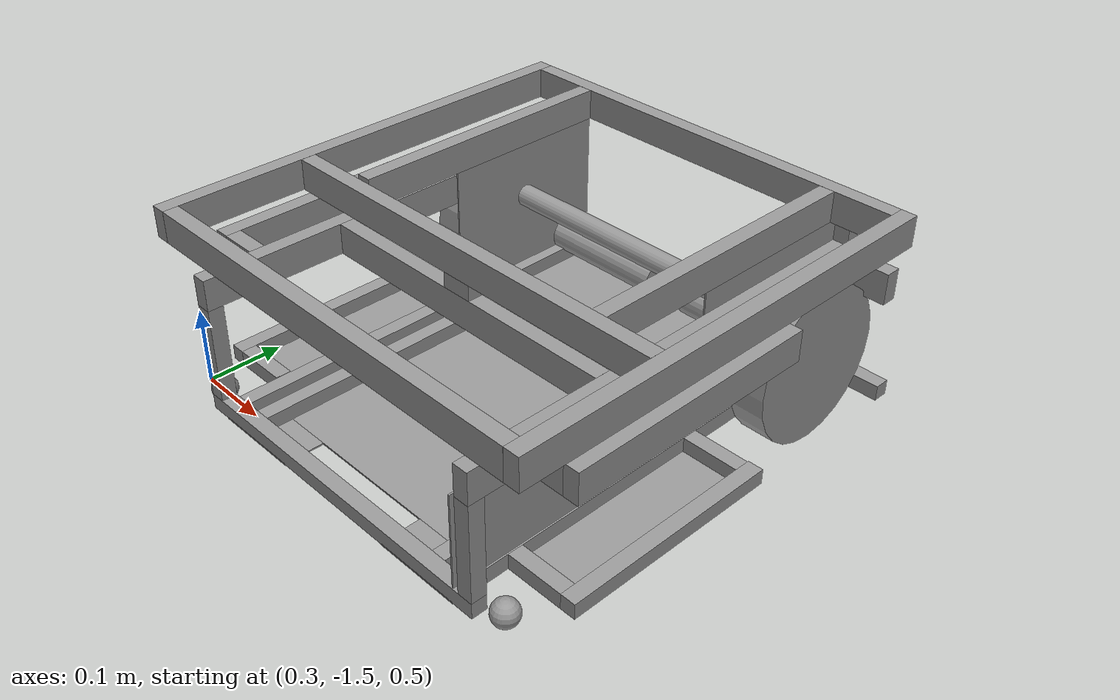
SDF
<?xml version='1.0'?>
<sdf version='1.6'>
  <model name='robotics_project'>
    <link name='base_plate_main'>
      <pose frame=''>0.582512 -1.20167 0.500001 0 -0 0</pose>
      <inertial>
        <mass>1.14663</mass>
        <inertia>
          <ixx>0.166667</ixx>
          <ixy>0</ixy>
          <ixz>0</ixz>
          <iyy>0.166667</iyy>
          <iyz>0</iyz>
          <izz>0.166667</izz>
        </inertia>
        <pose frame=''>0 0 0 0 -0 0</pose>
      </inertial>
      <self_collide>0</self_collide>
      <kinematic>0</kinematic>
      <visual name='visual'>
        <pose frame=''>0 0 0 0 -0 0</pose>
        <geometry>
          <box>
            <size>0.406 0.543 0.002</size>
          </box>
        </geometry>
        <material>
          <lighting>1</lighting>
          <script>
            <uri>file://media/materials/scripts/gazebo.material</uri>
            <name>Gazebo/Grey</name>
          </script>
          <shader type='pixel'>
            <normal_map>__default__</normal_map>
          </shader>
          <ambient>0.3 0.3 0.3 1</ambient>
          <diffuse>0.7 0.7 0.7 1</diffuse>
          <specular>0.01 0.01 0.01 1</specular>
          <emissive>0 0 0 1</emissive>
        </material>
        <transparency>0</transparency>
        <cast_shadows>1</cast_shadows>
      </visual>
      <collision name='collision'>
        <laser_retro>0</laser_retro>
        <max_contacts>10</max_contacts>
        <pose frame=''>0 0 0 0 -0 0</pose>
        <geometry>
          <box>
            <size>0.406 0.543 0.002</size>
          </box>
        </geometry>
        <surface>
          <friction>
            <ode>
              <mu>1</mu>
              <mu2>1</mu2>
              <fdir1>0 0 0</fdir1>
              <slip1>0</slip1>
              <slip2>0</slip2>
            </ode>
            <torsional>
              <coefficient>1</coefficient>
              <patch_radius>0</patch_radius>
              <surface_radius>0</surface_radius>
              <use_patch_radius>1</use_patch_radius>
              <ode>
                <slip>0</slip>
              </ode>
            </torsional>
          </friction>
          <bounce>
            <restitution_coefficient>0</restitution_coefficient>
            <threshold>1e+06</threshold>
          </bounce>
          <contact>
            <collide_without_contact>0</collide_without_contact>
            <collide_without_contact_bitmask>1</collide_without_contact_bitmask>
            <collide_bitmask>1</collide_bitmask>
            <ode>
              <soft_cfm>0</soft_cfm>
              <soft_erp>0.2</soft_erp>
              <kp>1e+13</kp>
              <kd>1</kd>
              <max_vel>0.01</max_vel>
              <min_depth>0</min_depth>
            </ode>
            <bullet>
              <split_impulse>1</split_impulse>
              <split_impulse_penetration_threshold>-0.01</split_impulse_penetration_threshold>
              <soft_cfm>0</soft_cfm>
              <soft_erp>0.2</soft_erp>
              <kp>1e+13</kp>
              <kd>1</kd>
            </bullet>
          </contact>
        </surface>
      </collision>
    </link>
    <link name='20X20_1'>
      <pose frame=''>0.361501 -0.936171 0.612477 0 1.5706 4e-06</pose>
      <inertial>
        <mass>0.091</mass>
        <inertia>
          <ixx>0.166667</ixx>
          <ixy>0</ixy>
          <ixz>0</ixz>
          <iyy>0.166667</iyy>
          <iyz>0</iyz>
          <izz>0.166667</izz>
        </inertia>
        <pose frame=''>0 0 0 0 -0 0</pose>
      </inertial>
      <self_collide>0</self_collide>
      <kinematic>0</kinematic>
      <visual name='visual'>
        <pose frame=''>0 0 0 0 -0 0</pose>
        <geometry>
          <box>
            <size>0.185 0.02 0.02</size>
          </box>
        </geometry>
        <material>
          <lighting>1</lighting>
          <script>
            <uri>file://media/materials/scripts/gazebo.material</uri>
            <name>Gazebo/Grey</name>
          </script>
          <shader type='pixel'>
            <normal_map>__default__</normal_map>
          </shader>
          <ambient>0.3 0.3 0.3 1</ambient>
          <diffuse>0.7 0.7 0.7 1</diffuse>
          <specular>0.01 0.01 0.01 1</specular>
          <emissive>0 0 0 1</emissive>
        </material>
        <transparency>0</transparency>
        <cast_shadows>1</cast_shadows>
      </visual>
      <collision name='collision'>
        <laser_retro>0</laser_retro>
        <max_contacts>10</max_contacts>
        <pose frame=''>0 0 0 0 -0 0</pose>
        <geometry>
          <box>
            <size>0.185 0.02 0.02</size>
          </box>
        </geometry>
        <surface>
          <friction>
            <ode>
              <mu>1</mu>
              <mu2>1</mu2>
              <fdir1>0 0 0</fdir1>
              <slip1>0</slip1>
              <slip2>0</slip2>
            </ode>
            <torsional>
              <coefficient>1</coefficient>
              <patch_radius>0</patch_radius>
              <surface_radius>0</surface_radius>
              <use_patch_radius>1</use_patch_radius>
              <ode>
                <slip>0</slip>
              </ode>
            </torsional>
          </friction>
          <bounce>
            <restitution_coefficient>0</restitution_coefficient>
            <threshold>1e+06</threshold>
          </bounce>
          <contact>
            <collide_without_contact>0</collide_without_contact>
            <collide_without_contact_bitmask>1</collide_without_contact_bitmask>
            <collide_bitmask>1</collide_bitmask>
            <ode>
              <soft_cfm>0</soft_cfm>
              <soft_erp>0.2</soft_erp>
              <kp>1e+13</kp>
              <kd>1</kd>
              <max_vel>0.01</max_vel>
              <min_depth>0</min_depth>
            </ode>
            <bullet>
              <split_impulse>1</split_impulse>
              <split_impulse_penetration_threshold>-0.01</split_impulse_penetration_threshold>
              <soft_cfm>0</soft_cfm>
              <soft_erp>0.2</soft_erp>
              <kp>1e+13</kp>
              <kd>1</kd>
            </bullet>
          </contact>
        </surface>
      </collision>
    </link>
    <link name='20X20_1_clone'>
      <pose frame=''>0.803501 -0.936171 0.612523 -1.1e-05 1.5706 -2.2e-05</pose>
      <inertial>
        <mass>0.091</mass>
        <inertia>
          <ixx>0.166667</ixx>
          <ixy>0</ixy>
          <ixz>0</ixz>
          <iyy>0.166667</iyy>
          <iyz>0</iyz>
          <izz>0.166667</izz>
        </inertia>
        <pose frame=''>0 0 0 0 -0 0</pose>
      </inertial>
      <self_collide>0</self_collide>
      <kinematic>0</kinematic>
      <visual name='visual'>
        <pose frame=''>0 0 0 0 -0 0</pose>
        <geometry>
          <box>
            <size>0.185 0.02 0.02</size>
          </box>
        </geometry>
        <material>
          <lighting>1</lighting>
          <script>
            <uri>file://media/materials/scripts/gazebo.material</uri>
            <name>Gazebo/Grey</name>
          </script>
          <shader type='pixel'>
            <normal_map>__default__</normal_map>
          </shader>
          <ambient>0.3 0.3 0.3 1</ambient>
          <diffuse>0.7 0.7 0.7 1</diffuse>
          <specular>0.01 0.01 0.01 1</specular>
          <emissive>0 0 0 1</emissive>
        </material>
        <transparency>0</transparency>
        <cast_shadows>1</cast_shadows>
      </visual>
      <collision name='collision'>
        <laser_retro>0</laser_retro>
        <max_contacts>10</max_contacts>
        <pose frame=''>0 0 0 0 -0 0</pose>
        <geometry>
          <box>
            <size>0.185 0.02 0.02</size>
          </box>
        </geometry>
        <surface>
          <friction>
            <ode>
              <mu>1</mu>
              <mu2>1</mu2>
              <fdir1>0 0 0</fdir1>
              <slip1>0</slip1>
              <slip2>0</slip2>
            </ode>
            <torsional>
              <coefficient>1</coefficient>
              <patch_radius>0</patch_radius>
              <surface_radius>0</surface_radius>
              <use_patch_radius>1</use_patch_radius>
              <ode>
                <slip>0</slip>
              </ode>
            </torsional>
          </friction>
          <bounce>
            <restitution_coefficient>0</restitution_coefficient>
            <threshold>1e+06</threshold>
          </bounce>
          <contact>
            <collide_without_contact>0</collide_without_contact>
            <collide_without_contact_bitmask>1</collide_without_contact_bitmask>
            <collide_bitmask>1</collide_bitmask>
            <ode>
              <soft_cfm>0</soft_cfm>
              <soft_erp>0.2</soft_erp>
              <kp>1e+13</kp>
              <kd>1</kd>
              <max_vel>0.01</max_vel>
              <min_depth>0</min_depth>
            </ode>
            <bullet>
              <split_impulse>1</split_impulse>
              <split_impulse_penetration_threshold>-0.01</split_impulse_penetration_threshold>
              <soft_cfm>0</soft_cfm>
              <soft_erp>0.2</soft_erp>
              <kp>1e+13</kp>
              <kd>1</kd>
            </bullet>
          </contact>
        </surface>
      </collision>
    </link>
    <link name='20X20_2_clone'>
      <pose frame=''>0.582512 -1.51617 0.510001 0 -0.000104 0</pose>
      <inertial>
        <mass>0.228</mass>
        <inertia>
          <ixx>0.166667</ixx>
          <ixy>0</ixy>
          <ixz>0</ixz>
          <iyy>0.166667</iyy>
          <iyz>0</iyz>
          <izz>0.166667</izz>
        </inertia>
        <pose frame=''>0 0 0 0 -0 0</pose>
      </inertial>
      <self_collide>0</self_collide>
      <kinematic>0</kinematic>
      <visual name='visual_0'>
        <pose frame=''>0 0 0 0 -0 0</pose>
        <geometry>
          <box>
            <size>0.462 0.02 0.02</size>
          </box>
        </geometry>
        <material>
          <lighting>1</lighting>
          <script>
            <uri>file://media/materials/scripts/gazebo.material</uri>
            <name>Gazebo/Grey</name>
          </script>
          <shader type='pixel'>
            <normal_map>__default__</normal_map>
          </shader>
          <ambient>0.3 0.3 0.3 1</ambient>
          <diffuse>0.7 0.7 0.7 1</diffuse>
          <specular>0.01 0.01 0.01 1</specular>
          <emissive>0 0 0 1</emissive>
        </material>
        <transparency>0</transparency>
        <cast_shadows>1</cast_shadows>
      </visual>
      <collision name='collision'>
        <laser_retro>0</laser_retro>
        <max_contacts>10</max_contacts>
        <pose frame=''>0 0 0 0 -0 0</pose>
        <geometry>
          <box>
            <size>0.462 0.02 0.02</size>
          </box>
        </geometry>
        <surface>
          <friction>
            <ode>
              <mu>1</mu>
              <mu2>1</mu2>
              <fdir1>0 0 0</fdir1>
              <slip1>0</slip1>
              <slip2>0</slip2>
            </ode>
            <torsional>
              <coefficient>1</coefficient>
              <patch_radius>0</patch_radius>
              <surface_radius>0</surface_radius>
              <use_patch_radius>1</use_patch_radius>
              <ode>
                <slip>0</slip>
              </ode>
            </torsional>
          </friction>
          <bounce>
            <restitution_coefficient>0</restitution_coefficient>
            <threshold>1e+06</threshold>
          </bounce>
          <contact>
            <collide_without_contact>0</collide_without_contact>
            <collide_without_contact_bitmask>1</collide_without_contact_bitmask>
            <collide_bitmask>1</collide_bitmask>
            <ode>
              <soft_cfm>0</soft_cfm>
              <soft_erp>0.2</soft_erp>
              <kp>1e+13</kp>
              <kd>1</kd>
              <max_vel>0.01</max_vel>
              <min_depth>0</min_depth>
            </ode>
            <bullet>
              <split_impulse>1</split_impulse>
              <split_impulse_penetration_threshold>-0.01</split_impulse_penetration_threshold>
              <soft_cfm>0</soft_cfm>
              <soft_erp>0.2</soft_erp>
              <kp>1e+13</kp>
              <kd>1</kd>
            </bullet>
          </contact>
        </surface>
      </collision>
    </link>
    <link name='20X20_2_clone_0'>
      <pose frame=''>0.582512 -0.936171 0.51 0 -0.000104 0</pose>
      <inertial>
        <mass>0.296</mass>
        <inertia>
          <ixx>0.166667</ixx>
          <ixy>0</ixy>
          <ixz>0</ixz>
          <iyy>0.166667</iyy>
          <iyz>0</iyz>
          <izz>0.166667</izz>
        </inertia>
        <pose frame=''>0 0 0 0 -0 0</pose>
      </inertial>
      <self_collide>0</self_collide>
      <kinematic>0</kinematic>
      <visual name='visual_0'>
        <pose frame=''>0 0 0 0 -0 0</pose>
        <geometry>
          <box>
            <size>0.6 0.02 0.02</size>
          </box>
        </geometry>
        <material>
          <lighting>1</lighting>
          <script>
            <uri>file://media/materials/scripts/gazebo.material</uri>
            <name>Gazebo/Grey</name>
          </script>
          <shader type='pixel'>
            <normal_map>__default__</normal_map>
          </shader>
          <ambient>0.3 0.3 0.3 1</ambient>
          <diffuse>0.7 0.7 0.7 1</diffuse>
          <specular>0.01 0.01 0.01 1</specular>
          <emissive>0 0 0 1</emissive>
        </material>
        <transparency>0</transparency>
        <cast_shadows>1</cast_shadows>
      </visual>
      <collision name='collision'>
        <laser_retro>0</laser_retro>
        <max_contacts>10</max_contacts>
        <pose frame=''>0 0 0 0 -0 0</pose>
        <geometry>
          <box>
            <size>0.6 0.02 0.02</size>
          </box>
        </geometry>
        <surface>
          <friction>
            <ode>
              <mu>1</mu>
              <mu2>1</mu2>
              <fdir1>0 0 0</fdir1>
              <slip1>0</slip1>
              <slip2>0</slip2>
            </ode>
            <torsional>
              <coefficient>1</coefficient>
              <patch_radius>0</patch_radius>
              <surface_radius>0</surface_radius>
              <use_patch_radius>1</use_patch_radius>
              <ode>
                <slip>0</slip>
              </ode>
            </torsional>
          </friction>
          <bounce>
            <restitution_coefficient>0</restitution_coefficient>
            <threshold>1e+06</threshold>
          </bounce>
          <contact>
            <collide_without_contact>0</collide_without_contact>
            <collide_without_contact_bitmask>1</collide_without_contact_bitmask>
            <collide_bitmask>1</collide_bitmask>
            <ode>
              <soft_cfm>0</soft_cfm>
              <soft_erp>0.2</soft_erp>
              <kp>1e+13</kp>
              <kd>1</kd>
              <max_vel>0.01</max_vel>
              <min_depth>0</min_depth>
            </ode>
            <bullet>
              <split_impulse>1</split_impulse>
              <split_impulse_penetration_threshold>-0.01</split_impulse_penetration_threshold>
              <soft_cfm>0</soft_cfm>
              <soft_erp>0.2</soft_erp>
              <kp>1e+13</kp>
              <kd>1</kd>
            </bullet>
          </contact>
        </surface>
      </collision>
    </link>
    <link name='20X20_3'>
      <pose frame=''>0.361504 -1.51617 0.582477 0.000451 1.5706 -8e-06</pose>
      <inertial>
        <mass>0.062</mass>
        <inertia>
          <ixx>0.166667</ixx>
          <ixy>0</ixy>
          <ixz>0</ixz>
          <iyy>0.166667</iyy>
          <iyz>0</iyz>
          <izz>0.166667</izz>
        </inertia>
        <pose frame=''>0 0 0 0 -0 0</pose>
      </inertial>
      <self_collide>0</self_collide>
      <kinematic>0</kinematic>
      <visual name='visual_0'>
        <pose frame=''>0 0 0 0 -0 0</pose>
        <geometry>
          <box>
            <size>0.125 0.02 0.02</size>
          </box>
        </geometry>
        <material>
          <lighting>1</lighting>
          <script>
            <uri>file://media/materials/scripts/gazebo.material</uri>
            <name>Gazebo/Grey</name>
          </script>
          <shader type='pixel'>
            <normal_map>__default__</normal_map>
          </shader>
          <ambient>0.3 0.3 0.3 1</ambient>
          <diffuse>0.7 0.7 0.7 1</diffuse>
          <specular>0.01 0.01 0.01 1</specular>
          <emissive>0 0 0 1</emissive>
        </material>
        <transparency>0</transparency>
        <cast_shadows>1</cast_shadows>
      </visual>
      <collision name='collision'>
        <laser_retro>0</laser_retro>
        <max_contacts>10</max_contacts>
        <pose frame=''>0 0 0 0 -0 0</pose>
        <geometry>
          <box>
            <size>0.125 0.02 0.02</size>
          </box>
        </geometry>
        <surface>
          <friction>
            <ode>
              <mu>1</mu>
              <mu2>1</mu2>
              <fdir1>0 0 0</fdir1>
              <slip1>0</slip1>
              <slip2>0</slip2>
            </ode>
            <torsional>
              <coefficient>1</coefficient>
              <patch_radius>0</patch_radius>
              <surface_radius>0</surface_radius>
              <use_patch_radius>1</use_patch_radius>
              <ode>
                <slip>0</slip>
              </ode>
            </torsional>
          </friction>
          <bounce>
            <restitution_coefficient>0</restitution_coefficient>
            <threshold>1e+06</threshold>
          </bounce>
          <contact>
            <collide_without_contact>0</collide_without_contact>
            <collide_without_contact_bitmask>1</collide_without_contact_bitmask>
            <collide_bitmask>1</collide_bitmask>
            <ode>
              <soft_cfm>0</soft_cfm>
              <soft_erp>0.2</soft_erp>
              <kp>1e+13</kp>
              <kd>1</kd>
              <max_vel>0.01</max_vel>
              <min_depth>0</min_depth>
            </ode>
            <bullet>
              <split_impulse>1</split_impulse>
              <split_impulse_penetration_threshold>-0.01</split_impulse_penetration_threshold>
              <soft_cfm>0</soft_cfm>
              <soft_erp>0.2</soft_erp>
              <kp>1e+13</kp>
              <kd>1</kd>
            </bullet>
          </contact>
        </surface>
      </collision>
    </link>
    <link name='20X20_3_clone'>
      <pose frame=''>0.803504 -1.51617 0.582523 8e-06 1.5706 8e-06</pose>
      <inertial>
        <mass>0.062</mass>
        <inertia>
          <ixx>0.166667</ixx>
          <ixy>0</ixy>
          <ixz>0</ixz>
          <iyy>0.166667</iyy>
          <iyz>0</iyz>
          <izz>0.166667</izz>
        </inertia>
        <pose frame=''>0 0 0 0 -0 0</pose>
      </inertial>
      <self_collide>0</self_collide>
      <kinematic>0</kinematic>
      <visual name='visual_0'>
        <pose frame=''>0 0 0 0 -0 0</pose>
        <geometry>
          <box>
            <size>0.125 0.02 0.02</size>
          </box>
        </geometry>
        <material>
          <lighting>1</lighting>
          <script>
            <uri>file://media/materials/scripts/gazebo.material</uri>
            <name>Gazebo/Grey</name>
          </script>
          <shader type='pixel'>
            <normal_map>__default__</normal_map>
          </shader>
          <ambient>0.3 0.3 0.3 1</ambient>
          <diffuse>0.7 0.7 0.7 1</diffuse>
          <specular>0.01 0.01 0.01 1</specular>
          <emissive>0 0 0 1</emissive>
        </material>
        <transparency>0</transparency>
        <cast_shadows>1</cast_shadows>
      </visual>
      <collision name='collision'>
        <laser_retro>0</laser_retro>
        <max_contacts>10</max_contacts>
        <pose frame=''>0 0 0 0 -0 0</pose>
        <geometry>
          <box>
            <size>0.125 0.02 0.02</size>
          </box>
        </geometry>
        <surface>
          <friction>
            <ode>
              <mu>1</mu>
              <mu2>1</mu2>
              <fdir1>0 0 0</fdir1>
              <slip1>0</slip1>
              <slip2>0</slip2>
            </ode>
            <torsional>
              <coefficient>1</coefficient>
              <patch_radius>0</patch_radius>
              <surface_radius>0</surface_radius>
              <use_patch_radius>1</use_patch_radius>
              <ode>
                <slip>0</slip>
              </ode>
            </torsional>
          </friction>
          <bounce>
            <restitution_coefficient>0</restitution_coefficient>
            <threshold>1e+06</threshold>
          </bounce>
          <contact>
            <collide_without_contact>0</collide_without_contact>
            <collide_without_contact_bitmask>1</collide_without_contact_bitmask>
            <collide_bitmask>1</collide_bitmask>
            <ode>
              <soft_cfm>0</soft_cfm>
              <soft_erp>0.2</soft_erp>
              <kp>1e+13</kp>
              <kd>1</kd>
              <max_vel>0.01</max_vel>
              <min_depth>0</min_depth>
            </ode>
            <bullet>
              <split_impulse>1</split_impulse>
              <split_impulse_penetration_threshold>-0.01</split_impulse_penetration_threshold>
              <soft_cfm>0</soft_cfm>
              <soft_erp>0.2</soft_erp>
              <kp>1e+13</kp>
              <kd>1</kd>
            </bullet>
          </contact>
        </surface>
      </collision>
    </link>
    <link name='20X20_4_clone'>
      <pose frame=''>0.872491 -1.30917 0.51003 -0.000104 -0 1.5707</pose>
      <inertial>
        <mass>0.143</mass>
        <inertia>
          <ixx>0.166667</ixx>
          <ixy>0</ixy>
          <ixz>0</ixz>
          <iyy>0.166667</iyy>
          <iyz>0</iyz>
          <izz>0.166667</izz>
        </inertia>
        <pose frame=''>0 0 0 0 -0 0</pose>
      </inertial>
      <self_collide>0</self_collide>
      <kinematic>0</kinematic>
      <visual name='visual_0'>
        <pose frame=''>0 0 0 0 -0 0</pose>
        <geometry>
          <box>
            <size>0.29 0.02 0.02</size>
          </box>
        </geometry>
        <material>
          <lighting>1</lighting>
          <script>
            <uri>file://media/materials/scripts/gazebo.material</uri>
            <name>Gazebo/Grey</name>
          </script>
          <shader type='pixel'>
            <normal_map>__default__</normal_map>
          </shader>
          <ambient>0.3 0.3 0.3 1</ambient>
          <diffuse>0.7 0.7 0.7 1</diffuse>
          <specular>0.01 0.01 0.01 1</specular>
          <emissive>0 0 0 1</emissive>
        </material>
        <transparency>0</transparency>
        <cast_shadows>1</cast_shadows>
      </visual>
      <collision name='collision'>
        <laser_retro>0</laser_retro>
        <max_contacts>10</max_contacts>
        <pose frame=''>0 0 0 0 -0 0</pose>
        <geometry>
          <box>
            <size>0.29 0.02 0.02</size>
          </box>
        </geometry>
        <surface>
          <friction>
            <ode>
              <mu>1</mu>
              <mu2>1</mu2>
              <fdir1>0 0 0</fdir1>
              <slip1>0</slip1>
              <slip2>0</slip2>
            </ode>
            <torsional>
              <coefficient>1</coefficient>
              <patch_radius>0</patch_radius>
              <surface_radius>0</surface_radius>
              <use_patch_radius>1</use_patch_radius>
              <ode>
                <slip>0</slip>
              </ode>
            </torsional>
          </friction>
          <bounce>
            <restitution_coefficient>0</restitution_coefficient>
            <threshold>1e+06</threshold>
          </bounce>
          <contact>
            <collide_without_contact>0</collide_without_contact>
            <collide_without_contact_bitmask>1</collide_without_contact_bitmask>
            <collide_bitmask>1</collide_bitmask>
            <ode>
              <soft_cfm>0</soft_cfm>
              <soft_erp>0.2</soft_erp>
              <kp>1e+13</kp>
              <kd>1</kd>
              <max_vel>0.01</max_vel>
              <min_depth>0</min_depth>
            </ode>
            <bullet>
              <split_impulse>1</split_impulse>
              <split_impulse_penetration_threshold>-0.01</split_impulse_penetration_threshold>
              <soft_cfm>0</soft_cfm>
              <soft_erp>0.2</soft_erp>
              <kp>1e+13</kp>
              <kd>1</kd>
            </bullet>
          </contact>
        </surface>
      </collision>
    </link>
    <link name='20X20_4_clone_clone'>
      <pose frame=''>0.291517 -1.30916 0.50997 0.000104 -0 -1.57109</pose>
      <inertial>
        <mass>0.143</mass>
        <inertia>
          <ixx>0.166667</ixx>
          <ixy>0</ixy>
          <ixz>0</ixz>
          <iyy>0.166667</iyy>
          <iyz>0</iyz>
          <izz>0.166667</izz>
        </inertia>
        <pose frame=''>0 0 0 0 -0 0</pose>
      </inertial>
      <self_collide>0</self_collide>
      <kinematic>0</kinematic>
      <visual name='visual_0'>
        <pose frame=''>0 0 0 0 -0 0</pose>
        <geometry>
          <box>
            <size>0.29 0.02 0.02</size>
          </box>
        </geometry>
        <material>
          <lighting>1</lighting>
          <script>
            <uri>file://media/materials/scripts/gazebo.material</uri>
            <name>Gazebo/Grey</name>
          </script>
          <shader type='pixel'>
            <normal_map>__default__</normal_map>
          </shader>
          <ambient>0.3 0.3 0.3 1</ambient>
          <diffuse>0.7 0.7 0.7 1</diffuse>
          <specular>0.01 0.01 0.01 1</specular>
          <emissive>0 0 0 1</emissive>
        </material>
        <transparency>0</transparency>
        <cast_shadows>1</cast_shadows>
      </visual>
      <collision name='collision'>
        <laser_retro>0</laser_retro>
        <max_contacts>10</max_contacts>
        <pose frame=''>0 0 0 0 -0 0</pose>
        <geometry>
          <box>
            <size>0.29 0.02 0.02</size>
          </box>
        </geometry>
        <surface>
          <friction>
            <ode>
              <mu>1</mu>
              <mu2>1</mu2>
              <fdir1>0 0 0</fdir1>
              <slip1>0</slip1>
              <slip2>0</slip2>
            </ode>
            <torsional>
              <coefficient>1</coefficient>
              <patch_radius>0</patch_radius>
              <surface_radius>0</surface_radius>
              <use_patch_radius>1</use_patch_radius>
              <ode>
                <slip>0</slip>
              </ode>
            </torsional>
          </friction>
          <bounce>
            <restitution_coefficient>0</restitution_coefficient>
            <threshold>1e+06</threshold>
          </bounce>
          <contact>
            <collide_without_contact>0</collide_without_contact>
            <collide_without_contact_bitmask>1</collide_without_contact_bitmask>
            <collide_bitmask>1</collide_bitmask>
            <ode>
              <soft_cfm>0</soft_cfm>
              <soft_erp>0.2</soft_erp>
              <kp>1e+13</kp>
              <kd>1</kd>
              <max_vel>0.01</max_vel>
              <min_depth>0</min_depth>
            </ode>
            <bullet>
              <split_impulse>1</split_impulse>
              <split_impulse_penetration_threshold>-0.01</split_impulse_penetration_threshold>
              <soft_cfm>0</soft_cfm>
              <soft_erp>0.2</soft_erp>
              <kp>1e+13</kp>
              <kd>1</kd>
            </bullet>
          </contact>
        </surface>
      </collision>
    </link>
    <link name='20X20_5_clone'>
      <pose frame=''>0.387512 -1.22617 0.50998 -0.000104 -0 1.5707</pose>
      <inertial>
        <mass>0.277</mass>
        <inertia>
          <ixx>0.166667</ixx>
          <ixy>0</ixy>
          <ixz>0</ixz>
          <iyy>0.166667</iyy>
          <iyz>0</iyz>
          <izz>0.166667</izz>
        </inertia>
        <pose frame=''>0 0 0 0 -0 0</pose>
      </inertial>
      <self_collide>0</self_collide>
      <kinematic>0</kinematic>
      <visual name='visual_0'>
        <pose frame=''>0 0 0 0 -0 0</pose>
        <geometry>
          <box>
            <size>0.56 0.02 0.02</size>
          </box>
        </geometry>
        <material>
          <lighting>1</lighting>
          <script>
            <uri>file://media/materials/scripts/gazebo.material</uri>
            <name>Gazebo/Grey</name>
          </script>
          <shader type='pixel'>
            <normal_map>__default__</normal_map>
          </shader>
          <ambient>0.3 0.3 0.3 1</ambient>
          <diffuse>0.7 0.7 0.7 1</diffuse>
          <specular>0.01 0.01 0.01 1</specular>
          <emissive>0 0 0 1</emissive>
        </material>
        <transparency>0</transparency>
        <cast_shadows>1</cast_shadows>
      </visual>
      <collision name='collision'>
        <laser_retro>0</laser_retro>
        <max_contacts>10</max_contacts>
        <pose frame=''>0 0 0 0 -0 0</pose>
        <geometry>
          <box>
            <size>0.56 0.02 0.02</size>
          </box>
        </geometry>
        <surface>
          <friction>
            <ode>
              <mu>1</mu>
              <mu2>1</mu2>
              <fdir1>0 0 0</fdir1>
              <slip1>0</slip1>
              <slip2>0</slip2>
            </ode>
            <torsional>
              <coefficient>1</coefficient>
              <patch_radius>0</patch_radius>
              <surface_radius>0</surface_radius>
              <use_patch_radius>1</use_patch_radius>
              <ode>
                <slip>0</slip>
              </ode>
            </torsional>
          </friction>
          <bounce>
            <restitution_coefficient>0</restitution_coefficient>
            <threshold>1e+06</threshold>
          </bounce>
          <contact>
            <collide_without_contact>0</collide_without_contact>
            <collide_without_contact_bitmask>1</collide_without_contact_bitmask>
            <collide_bitmask>1</collide_bitmask>
            <ode>
              <soft_cfm>0</soft_cfm>
              <soft_erp>0.2</soft_erp>
              <kp>1e+13</kp>
              <kd>1</kd>
              <max_vel>0.01</max_vel>
              <min_depth>0</min_depth>
            </ode>
            <bullet>
              <split_impulse>1</split_impulse>
              <split_impulse_penetration_threshold>-0.01</split_impulse_penetration_threshold>
              <soft_cfm>0</soft_cfm>
              <soft_erp>0.2</soft_erp>
              <kp>1e+13</kp>
              <kd>1</kd>
            </bullet>
          </contact>
        </surface>
      </collision>
    </link>
    <link name='20X20_5_clone_clone'>
      <pose frame=''>0.777512 -1.22617 0.51002 -0.000104 -0 1.5707</pose>
      <inertial>
        <mass>0.277</mass>
        <inertia>
          <ixx>0.166667</ixx>
          <ixy>0</ixy>
          <ixz>0</ixz>
          <iyy>0.166667</iyy>
          <iyz>0</iyz>
          <izz>0.166667</izz>
        </inertia>
        <pose frame=''>0 0 0 0 -0 0</pose>
      </inertial>
      <self_collide>0</self_collide>
      <kinematic>0</kinematic>
      <visual name='visual_0'>
        <pose frame=''>0 0 0 0 -0 0</pose>
        <geometry>
          <box>
            <size>0.56 0.02 0.02</size>
          </box>
        </geometry>
        <material>
          <lighting>1</lighting>
          <script>
            <uri>file://media/materials/scripts/gazebo.material</uri>
            <name>Gazebo/Grey</name>
          </script>
          <shader type='pixel'>
            <normal_map>__default__</normal_map>
          </shader>
          <ambient>0.3 0.3 0.3 1</ambient>
          <diffuse>0.7 0.7 0.7 1</diffuse>
          <specular>0.01 0.01 0.01 1</specular>
          <emissive>0 0 0 1</emissive>
        </material>
        <transparency>0</transparency>
        <cast_shadows>1</cast_shadows>
      </visual>
      <collision name='collision'>
        <laser_retro>0</laser_retro>
        <max_contacts>10</max_contacts>
        <pose frame=''>0 0 0 0 -0 0</pose>
        <geometry>
          <box>
            <size>0.56 0.02 0.02</size>
          </box>
        </geometry>
        <surface>
          <friction>
            <ode>
              <mu>1</mu>
              <mu2>1</mu2>
              <fdir1>0 0 0</fdir1>
              <slip1>0</slip1>
              <slip2>0</slip2>
            </ode>
            <torsional>
              <coefficient>1</coefficient>
              <patch_radius>0</patch_radius>
              <surface_radius>0</surface_radius>
              <use_patch_radius>1</use_patch_radius>
              <ode>
                <slip>0</slip>
              </ode>
            </torsional>
          </friction>
          <bounce>
            <restitution_coefficient>0</restitution_coefficient>
            <threshold>1e+06</threshold>
          </bounce>
          <contact>
            <collide_without_contact>0</collide_without_contact>
            <collide_without_contact_bitmask>1</collide_without_contact_bitmask>
            <collide_bitmask>1</collide_bitmask>
            <ode>
              <soft_cfm>0</soft_cfm>
              <soft_erp>0.2</soft_erp>
              <kp>1e+13</kp>
              <kd>1</kd>
              <max_vel>0.01</max_vel>
              <min_depth>0</min_depth>
            </ode>
            <bullet>
              <split_impulse>1</split_impulse>
              <split_impulse_penetration_threshold>-0.01</split_impulse_penetration_threshold>
              <soft_cfm>0</soft_cfm>
              <soft_erp>0.2</soft_erp>
              <kp>1e+13</kp>
              <kd>1</kd>
            </bullet>
          </contact>
        </surface>
      </collision>
    </link>
    <link name='20X20_7_clone'>
      <pose frame=''>0.824991 -1.44417 0.510025 0 -0.000104 0</pose>
      <inertial>
        <mass>0.037</mass>
        <inertia>
          <ixx>0.166667</ixx>
          <ixy>0</ixy>
          <ixz>0</ixz>
          <iyy>0.166667</iyy>
          <iyz>0</iyz>
          <izz>0.166667</izz>
        </inertia>
        <pose frame=''>0 0 0 0 -0 0</pose>
      </inertial>
      <self_collide>0</self_collide>
      <kinematic>0</kinematic>
      <visual name='visual_0'>
        <pose frame=''>0 0 0 0 -0 0</pose>
        <geometry>
          <box>
            <size>0.075 0.02 0.02</size>
          </box>
        </geometry>
        <material>
          <lighting>1</lighting>
          <script>
            <uri>file://media/materials/scripts/gazebo.material</uri>
            <name>Gazebo/Grey</name>
          </script>
          <shader type='pixel'>
            <normal_map>__default__</normal_map>
          </shader>
          <ambient>0.3 0.3 0.3 1</ambient>
          <diffuse>0.7 0.7 0.7 1</diffuse>
          <specular>0.01 0.01 0.01 1</specular>
          <emissive>0 0 0 1</emissive>
        </material>
        <transparency>0</transparency>
        <cast_shadows>1</cast_shadows>
      </visual>
      <collision name='collision'>
        <laser_retro>0</laser_retro>
        <max_contacts>10</max_contacts>
        <pose frame=''>0 0 0 0 -0 0</pose>
        <geometry>
          <box>
            <size>0.075 0.02 0.02</size>
          </box>
        </geometry>
        <surface>
          <friction>
            <ode>
              <mu>1</mu>
              <mu2>1</mu2>
              <fdir1>0 0 0</fdir1>
              <slip1>0</slip1>
              <slip2>0</slip2>
            </ode>
            <torsional>
              <coefficient>1</coefficient>
              <patch_radius>0</patch_radius>
              <surface_radius>0</surface_radius>
              <use_patch_radius>1</use_patch_radius>
              <ode>
                <slip>0</slip>
              </ode>
            </torsional>
          </friction>
          <bounce>
            <restitution_coefficient>0</restitution_coefficient>
            <threshold>1e+06</threshold>
          </bounce>
          <contact>
            <collide_without_contact>0</collide_without_contact>
            <collide_without_contact_bitmask>1</collide_without_contact_bitmask>
            <collide_bitmask>1</collide_bitmask>
            <ode>
              <soft_cfm>0</soft_cfm>
              <soft_erp>0.2</soft_erp>
              <kp>1e+13</kp>
              <kd>1</kd>
              <max_vel>0.01</max_vel>
              <min_depth>0</min_depth>
            </ode>
            <bullet>
              <split_impulse>1</split_impulse>
              <split_impulse_penetration_threshold>-0.01</split_impulse_penetration_threshold>
              <soft_cfm>0</soft_cfm>
              <soft_erp>0.2</soft_erp>
              <kp>1e+13</kp>
              <kd>1</kd>
            </bullet>
          </contact>
        </surface>
      </collision>
    </link>
    <link name='20X20_7_clone_clone'>
      <pose frame=''>0.825017 -1.1759 0.510025 0 0.000104 3.1414</pose>
      <inertial>
        <mass>0.037</mass>
        <inertia>
          <ixx>0.166667</ixx>
          <ixy>0</ixy>
          <ixz>0</ixz>
          <iyy>0.166667</iyy>
          <iyz>0</iyz>
          <izz>0.166667</izz>
        </inertia>
        <pose frame=''>0 0 0 0 -0 0</pose>
      </inertial>
      <self_collide>0</self_collide>
      <kinematic>0</kinematic>
      <visual name='visual_0'>
        <pose frame=''>0 0 0 0 -0 0</pose>
        <geometry>
          <box>
            <size>0.075 0.02 0.02</size>
          </box>
        </geometry>
        <material>
          <lighting>1</lighting>
          <script>
            <uri>file://media/materials/scripts/gazebo.material</uri>
            <name>Gazebo/Grey</name>
          </script>
          <shader type='pixel'>
            <normal_map>__default__</normal_map>
          </shader>
          <ambient>0.3 0.3 0.3 1</ambient>
          <diffuse>0.7 0.7 0.7 1</diffuse>
          <specular>0.01 0.01 0.01 1</specular>
          <emissive>0 0 0 1</emissive>
        </material>
        <transparency>0</transparency>
        <cast_shadows>1</cast_shadows>
      </visual>
      <collision name='collision'>
        <laser_retro>0</laser_retro>
        <max_contacts>10</max_contacts>
        <pose frame=''>0 0 0 0 -0 0</pose>
        <geometry>
          <box>
            <size>0.075 0.02 0.02</size>
          </box>
        </geometry>
        <surface>
          <friction>
            <ode>
              <mu>1</mu>
              <mu2>1</mu2>
              <fdir1>0 0 0</fdir1>
              <slip1>0</slip1>
              <slip2>0</slip2>
            </ode>
            <torsional>
              <coefficient>1</coefficient>
              <patch_radius>0</patch_radius>
              <surface_radius>0</surface_radius>
              <use_patch_radius>1</use_patch_radius>
              <ode>
                <slip>0</slip>
              </ode>
            </torsional>
          </friction>
          <bounce>
            <restitution_coefficient>0</restitution_coefficient>
            <threshold>1e+06</threshold>
          </bounce>
          <contact>
            <collide_without_contact>0</collide_without_contact>
            <collide_without_contact_bitmask>1</collide_without_contact_bitmask>
            <collide_bitmask>1</collide_bitmask>
            <ode>
              <soft_cfm>0</soft_cfm>
              <soft_erp>0.2</soft_erp>
              <kp>1e+13</kp>
              <kd>1</kd>
              <max_vel>0.01</max_vel>
              <min_depth>0</min_depth>
            </ode>
            <bullet>
              <split_impulse>1</split_impulse>
              <split_impulse_penetration_threshold>-0.01</split_impulse_penetration_threshold>
              <soft_cfm>0</soft_cfm>
              <soft_erp>0.2</soft_erp>
              <kp>1e+13</kp>
              <kd>1</kd>
            </bullet>
          </contact>
        </surface>
      </collision>
    </link>
    <link name='20X20_7_clone_clone_0'>
      <pose frame=''>0.339017 -1.17867 0.509975 0 0.000104 3.1414</pose>
      <inertial>
        <mass>0.037</mass>
        <inertia>
          <ixx>0.166667</ixx>
          <ixy>0</ixy>
          <ixz>0</ixz>
          <iyy>0.166667</iyy>
          <iyz>0</iyz>
          <izz>0.166667</izz>
        </inertia>
        <pose frame=''>0 0 0 0 -0 0</pose>
      </inertial>
      <self_collide>0</self_collide>
      <kinematic>0</kinematic>
      <visual name='visual_0'>
        <pose frame=''>0 0 0 0 -0 0</pose>
        <geometry>
          <box>
            <size>0.075 0.02 0.02</size>
          </box>
        </geometry>
        <material>
          <lighting>1</lighting>
          <script>
            <uri>file://media/materials/scripts/gazebo.material</uri>
            <name>Gazebo/Grey</name>
          </script>
          <shader type='pixel'>
            <normal_map>__default__</normal_map>
          </shader>
          <ambient>0.3 0.3 0.3 1</ambient>
          <diffuse>0.7 0.7 0.7 1</diffuse>
          <specular>0.01 0.01 0.01 1</specular>
          <emissive>0 0 0 1</emissive>
        </material>
        <transparency>0</transparency>
        <cast_shadows>1</cast_shadows>
      </visual>
      <collision name='collision'>
        <laser_retro>0</laser_retro>
        <max_contacts>10</max_contacts>
        <pose frame=''>0 0 0 0 -0 0</pose>
        <geometry>
          <box>
            <size>0.075 0.02 0.02</size>
          </box>
        </geometry>
        <surface>
          <friction>
            <ode>
              <mu>1</mu>
              <mu2>1</mu2>
              <fdir1>0 0 0</fdir1>
              <slip1>0</slip1>
              <slip2>0</slip2>
            </ode>
            <torsional>
              <coefficient>1</coefficient>
              <patch_radius>0</patch_radius>
              <surface_radius>0</surface_radius>
              <use_patch_radius>1</use_patch_radius>
              <ode>
                <slip>0</slip>
              </ode>
            </torsional>
          </friction>
          <bounce>
            <restitution_coefficient>0</restitution_coefficient>
            <threshold>1e+06</threshold>
          </bounce>
          <contact>
            <collide_without_contact>0</collide_without_contact>
            <collide_without_contact_bitmask>1</collide_without_contact_bitmask>
            <collide_bitmask>1</collide_bitmask>
            <ode>
              <soft_cfm>0</soft_cfm>
              <soft_erp>0.2</soft_erp>
              <kp>1e+13</kp>
              <kd>1</kd>
              <max_vel>0.01</max_vel>
              <min_depth>0</min_depth>
            </ode>
            <bullet>
              <split_impulse>1</split_impulse>
              <split_impulse_penetration_threshold>-0.01</split_impulse_penetration_threshold>
              <soft_cfm>0</soft_cfm>
              <soft_erp>0.2</soft_erp>
              <kp>1e+13</kp>
              <kd>1</kd>
            </bullet>
          </contact>
        </surface>
      </collision>
    </link>
    <link name='20X20_7_clone_clone_0_clone'>
      <pose frame=''>0.338991 -1.44416 0.509975 0 0.000104 3.1414</pose>
      <inertial>
        <mass>0.037</mass>
        <inertia>
          <ixx>0.166667</ixx>
          <ixy>0</ixy>
          <ixz>0</ixz>
          <iyy>0.166667</iyy>
          <iyz>0</iyz>
          <izz>0.166667</izz>
        </inertia>
        <pose frame=''>0 0 0 0 -0 0</pose>
      </inertial>
      <self_collide>0</self_collide>
      <kinematic>0</kinematic>
      <visual name='visual_0'>
        <pose frame=''>0 0 0 0 -0 0</pose>
        <geometry>
          <box>
            <size>0.075 0.02 0.02</size>
          </box>
        </geometry>
        <material>
          <lighting>1</lighting>
          <script>
            <uri>file://media/materials/scripts/gazebo.material</uri>
            <name>Gazebo/Grey</name>
          </script>
          <shader type='pixel'>
            <normal_map>__default__</normal_map>
          </shader>
          <ambient>0.3 0.3 0.3 1</ambient>
          <diffuse>0.7 0.7 0.7 1</diffuse>
          <specular>0.01 0.01 0.01 1</specular>
          <emissive>0 0 0 1</emissive>
        </material>
        <transparency>0</transparency>
        <cast_shadows>1</cast_shadows>
      </visual>
      <collision name='collision'>
        <laser_retro>0</laser_retro>
        <max_contacts>10</max_contacts>
        <pose frame=''>0 0 0 0 -0 0</pose>
        <geometry>
          <box>
            <size>0.075 0.02 0.02</size>
          </box>
        </geometry>
        <surface>
          <friction>
            <ode>
              <mu>1</mu>
              <mu2>1</mu2>
              <fdir1>0 0 0</fdir1>
              <slip1>0</slip1>
              <slip2>0</slip2>
            </ode>
            <torsional>
              <coefficient>1</coefficient>
              <patch_radius>0</patch_radius>
              <surface_radius>0</surface_radius>
              <use_patch_radius>1</use_patch_radius>
              <ode>
                <slip>0</slip>
              </ode>
            </torsional>
          </friction>
          <bounce>
            <restitution_coefficient>0</restitution_coefficient>
            <threshold>1e+06</threshold>
          </bounce>
          <contact>
            <collide_without_contact>0</collide_without_contact>
            <collide_without_contact_bitmask>1</collide_without_contact_bitmask>
            <collide_bitmask>1</collide_bitmask>
            <ode>
              <soft_cfm>0</soft_cfm>
              <soft_erp>0.2</soft_erp>
              <kp>1e+13</kp>
              <kd>1</kd>
              <max_vel>0.01</max_vel>
              <min_depth>0</min_depth>
            </ode>
            <bullet>
              <split_impulse>1</split_impulse>
              <split_impulse_penetration_threshold>-0.01</split_impulse_penetration_threshold>
              <soft_cfm>0</soft_cfm>
              <soft_erp>0.2</soft_erp>
              <kp>1e+13</kp>
              <kd>1</kd>
            </bullet>
          </contact>
        </surface>
      </collision>
    </link>
    <link name='20X20_8_clone'>
      <pose frame=''>0.424512 -1.32117 0.509984 -0.000104 -0 1.5707</pose>
      <inertial>
        <mass>0.183</mass>
        <inertia>
          <ixx>0.166667</ixx>
          <ixy>0</ixy>
          <ixz>0</ixz>
          <iyy>0.166667</iyy>
          <iyz>0</iyz>
          <izz>0.166667</izz>
        </inertia>
        <pose frame=''>0 0 0 0 -0 0</pose>
      </inertial>
      <self_collide>0</self_collide>
      <kinematic>0</kinematic>
      <visual name='visual_0'>
        <pose frame=''>0 0 0 0 -0 0</pose>
        <geometry>
          <box>
            <size>0.37 0.02 0.02</size>
          </box>
        </geometry>
        <material>
          <lighting>1</lighting>
          <script>
            <uri>file://media/materials/scripts/gazebo.material</uri>
            <name>Gazebo/Grey</name>
          </script>
          <shader type='pixel'>
            <normal_map>__default__</normal_map>
          </shader>
          <ambient>0.3 0.3 0.3 1</ambient>
          <diffuse>0.7 0.7 0.7 1</diffuse>
          <specular>0.01 0.01 0.01 1</specular>
          <emissive>0 0 0 1</emissive>
        </material>
        <transparency>0</transparency>
        <cast_shadows>1</cast_shadows>
      </visual>
      <collision name='collision'>
        <laser_retro>0</laser_retro>
        <max_contacts>10</max_contacts>
        <pose frame=''>0 0 0 0 -0 0</pose>
        <geometry>
          <box>
            <size>0.37 0.02 0.02</size>
          </box>
        </geometry>
        <surface>
          <friction>
            <ode>
              <mu>1</mu>
              <mu2>1</mu2>
              <fdir1>0 0 0</fdir1>
              <slip1>0</slip1>
              <slip2>0</slip2>
            </ode>
            <torsional>
              <coefficient>1</coefficient>
              <patch_radius>0</patch_radius>
              <surface_radius>0</surface_radius>
              <use_patch_radius>1</use_patch_radius>
              <ode>
                <slip>0</slip>
              </ode>
            </torsional>
          </friction>
          <bounce>
            <restitution_coefficient>0</restitution_coefficient>
            <threshold>1e+06</threshold>
          </bounce>
          <contact>
            <collide_without_contact>0</collide_without_contact>
            <collide_without_contact_bitmask>1</collide_without_contact_bitmask>
            <collide_bitmask>1</collide_bitmask>
            <ode>
              <soft_cfm>0</soft_cfm>
              <soft_erp>0.2</soft_erp>
              <kp>1e+13</kp>
              <kd>1</kd>
              <max_vel>0.01</max_vel>
              <min_depth>0</min_depth>
            </ode>
            <bullet>
              <split_impulse>1</split_impulse>
              <split_impulse_penetration_threshold>-0.01</split_impulse_penetration_threshold>
              <soft_cfm>0</soft_cfm>
              <soft_erp>0.2</soft_erp>
              <kp>1e+13</kp>
              <kd>1</kd>
            </bullet>
          </contact>
        </surface>
      </collision>
    </link>
    <link name='20X20_8_clone_0'>
      <pose frame=''>0.582512 -1.12617 0.51 0 -0.000104 0</pose>
      <inertial>
        <mass>0.183</mass>
        <inertia>
          <ixx>0.166667</ixx>
          <ixy>0</ixy>
          <ixz>0</ixz>
          <iyy>0.166667</iyy>
          <iyz>0</iyz>
          <izz>0.166667</izz>
        </inertia>
        <pose frame=''>0 0 0 0 -0 0</pose>
      </inertial>
      <self_collide>0</self_collide>
      <kinematic>0</kinematic>
      <visual name='visual_0'>
        <pose frame=''>0 0 0 0 -0 0</pose>
        <geometry>
          <box>
            <size>0.37 0.02 0.02</size>
          </box>
        </geometry>
        <material>
          <lighting>1</lighting>
          <script>
            <uri>file://media/materials/scripts/gazebo.material</uri>
            <name>Gazebo/Grey</name>
          </script>
          <shader type='pixel'>
            <normal_map>__default__</normal_map>
          </shader>
          <ambient>0.3 0.3 0.3 1</ambient>
          <diffuse>0.7 0.7 0.7 1</diffuse>
          <specular>0.01 0.01 0.01 1</specular>
          <emissive>0 0 0 1</emissive>
        </material>
        <transparency>0</transparency>
        <cast_shadows>1</cast_shadows>
      </visual>
      <collision name='collision'>
        <laser_retro>0</laser_retro>
        <max_contacts>10</max_contacts>
        <pose frame=''>0 0 0 0 -0 0</pose>
        <geometry>
          <box>
            <size>0.37 0.02 0.02</size>
          </box>
        </geometry>
        <surface>
          <friction>
            <ode>
              <mu>1</mu>
              <mu2>1</mu2>
              <fdir1>0 0 0</fdir1>
              <slip1>0</slip1>
              <slip2>0</slip2>
            </ode>
            <torsional>
              <coefficient>1</coefficient>
              <patch_radius>0</patch_radius>
              <surface_radius>0</surface_radius>
              <use_patch_radius>1</use_patch_radius>
              <ode>
                <slip>0</slip>
              </ode>
            </torsional>
          </friction>
          <bounce>
            <restitution_coefficient>0</restitution_coefficient>
            <threshold>1e+06</threshold>
          </bounce>
          <contact>
            <collide_without_contact>0</collide_without_contact>
            <collide_without_contact_bitmask>1</collide_without_contact_bitmask>
            <collide_bitmask>1</collide_bitmask>
            <ode>
              <soft_cfm>0</soft_cfm>
              <soft_erp>0.2</soft_erp>
              <kp>1e+13</kp>
              <kd>1</kd>
              <max_vel>0.01</max_vel>
              <min_depth>0</min_depth>
            </ode>
            <bullet>
              <split_impulse>1</split_impulse>
              <split_impulse_penetration_threshold>-0.01</split_impulse_penetration_threshold>
              <soft_cfm>0</soft_cfm>
              <soft_erp>0.2</soft_erp>
              <kp>1e+13</kp>
              <kd>1</kd>
            </bullet>
          </contact>
        </surface>
      </collision>
    </link>
    <link name='20X20_8_clone_clone'>
      <pose frame=''>0.740512 -1.32117 0.510016 -0.000104 -0 1.5707</pose>
      <inertial>
        <mass>0.183</mass>
        <inertia>
          <ixx>0.166667</ixx>
          <ixy>0</ixy>
          <ixz>0</ixz>
          <iyy>0.166667</iyy>
          <iyz>0</iyz>
          <izz>0.166667</izz>
        </inertia>
        <pose frame=''>0 0 0 0 -0 0</pose>
      </inertial>
      <self_collide>0</self_collide>
      <kinematic>0</kinematic>
      <visual name='visual_0'>
        <pose frame=''>0 0 0 0 -0 0</pose>
        <geometry>
          <box>
            <size>0.37 0.02 0.02</size>
          </box>
        </geometry>
        <material>
          <lighting>1</lighting>
          <script>
            <uri>file://media/materials/scripts/gazebo.material</uri>
            <name>Gazebo/Grey</name>
          </script>
          <shader type='pixel'>
            <normal_map>__default__</normal_map>
          </shader>
          <ambient>0.3 0.3 0.3 1</ambient>
          <diffuse>0.7 0.7 0.7 1</diffuse>
          <specular>0.01 0.01 0.01 1</specular>
          <emissive>0 0 0 1</emissive>
        </material>
        <transparency>0</transparency>
        <cast_shadows>1</cast_shadows>
      </visual>
      <collision name='collision'>
        <laser_retro>0</laser_retro>
        <max_contacts>10</max_contacts>
        <pose frame=''>0 0 0 0 -0 0</pose>
        <geometry>
          <box>
            <size>0.37 0.02 0.02</size>
          </box>
        </geometry>
        <surface>
          <friction>
            <ode>
              <mu>1</mu>
              <mu2>1</mu2>
              <fdir1>0 0 0</fdir1>
              <slip1>0</slip1>
              <slip2>0</slip2>
            </ode>
            <torsional>
              <coefficient>1</coefficient>
              <patch_radius>0</patch_radius>
              <surface_radius>0</surface_radius>
              <use_patch_radius>1</use_patch_radius>
              <ode>
                <slip>0</slip>
              </ode>
            </torsional>
          </friction>
          <bounce>
            <restitution_coefficient>0</restitution_coefficient>
            <threshold>1e+06</threshold>
          </bounce>
          <contact>
            <collide_without_contact>0</collide_without_contact>
            <collide_without_contact_bitmask>1</collide_without_contact_bitmask>
            <collide_bitmask>1</collide_bitmask>
            <ode>
              <soft_cfm>0</soft_cfm>
              <soft_erp>0.2</soft_erp>
              <kp>1e+13</kp>
              <kd>1</kd>
              <max_vel>0.01</max_vel>
              <min_depth>0</min_depth>
            </ode>
            <bullet>
              <split_impulse>1</split_impulse>
              <split_impulse_penetration_threshold>-0.01</split_impulse_penetration_threshold>
              <soft_cfm>0</soft_cfm>
              <soft_erp>0.2</soft_erp>
              <kp>1e+13</kp>
              <kd>1</kd>
            </bullet>
          </contact>
        </surface>
      </collision>
    </link>
    <link name='40X20_1_clone'>
      <pose frame=''>0.803488 -1.23617 0.665023 3.1413 9.6e-05 1.5708</pose>
      <inertial>
        <mass>0.518</mass>
        <inertia>
          <ixx>0.166667</ixx>
          <ixy>0</ixy>
          <ixz>0</ixz>
          <iyy>0.166667</iyy>
          <iyz>0</iyz>
          <izz>0.166667</izz>
        </inertia>
        <pose frame=''>0 0 0 0 -0 0</pose>
      </inertial>
      <self_collide>0</self_collide>
      <kinematic>0</kinematic>
      <visual name='visual'>
        <pose frame=''>0 0 0 0 -0 0</pose>
        <geometry>
          <box>
            <size>0.58 0.02 0.04</size>
          </box>
        </geometry>
        <material>
          <lighting>1</lighting>
          <script>
            <uri>file://media/materials/scripts/gazebo.material</uri>
            <name>Gazebo/Grey</name>
          </script>
          <shader type='pixel'>
            <normal_map>__default__</normal_map>
          </shader>
          <ambient>0.3 0.3 0.3 1</ambient>
          <diffuse>0.7 0.7 0.7 1</diffuse>
          <specular>0.01 0.01 0.01 1</specular>
          <emissive>0 0 0 1</emissive>
        </material>
        <transparency>0</transparency>
        <cast_shadows>1</cast_shadows>
      </visual>
      <collision name='collision'>
        <laser_retro>0</laser_retro>
        <max_contacts>10</max_contacts>
        <pose frame=''>0 0 0 0 -0 0</pose>
        <geometry>
          <box>
            <size>0.58 0.02 0.04</size>
          </box>
        </geometry>
        <surface>
          <friction>
            <ode>
              <mu>1</mu>
              <mu2>1</mu2>
              <fdir1>0 0 0</fdir1>
              <slip1>0</slip1>
              <slip2>0</slip2>
            </ode>
            <torsional>
              <coefficient>1</coefficient>
              <patch_radius>0</patch_radius>
              <surface_radius>0</surface_radius>
              <use_patch_radius>1</use_patch_radius>
              <ode>
                <slip>0</slip>
              </ode>
            </torsional>
          </friction>
          <bounce>
            <restitution_coefficient>0</restitution_coefficient>
            <threshold>1e+06</threshold>
          </bounce>
          <contact>
            <collide_without_contact>0</collide_without_contact>
            <collide_without_contact_bitmask>1</collide_without_contact_bitmask>
            <collide_bitmask>1</collide_bitmask>
            <ode>
              <soft_cfm>0</soft_cfm>
              <soft_erp>0.2</soft_erp>
              <kp>1e+13</kp>
              <kd>1</kd>
              <max_vel>0.01</max_vel>
              <min_depth>0</min_depth>
            </ode>
            <bullet>
              <split_impulse>1</split_impulse>
              <split_impulse_penetration_threshold>-0.01</split_impulse_penetration_threshold>
              <soft_cfm>0</soft_cfm>
              <soft_erp>0.2</soft_erp>
              <kp>1e+13</kp>
              <kd>1</kd>
            </bullet>
          </contact>
        </surface>
      </collision>
    </link>
    <link name='40X20_1_clone_0'>
      <pose frame=''>0.361488 -1.23617 0.664894 3.1413 9.6e-05 1.5708</pose>
      <inertial>
        <mass>0.518</mass>
        <inertia>
          <ixx>0.166667</ixx>
          <ixy>0</ixy>
          <ixz>0</ixz>
          <iyy>0.166667</iyy>
          <iyz>0</iyz>
          <izz>0.166667</izz>
        </inertia>
        <pose frame=''>0 0 0 0 -0 0</pose>
      </inertial>
      <self_collide>0</self_collide>
      <kinematic>0</kinematic>
      <visual name='visual'>
        <pose frame=''>0 0 0 0 -0 0</pose>
        <geometry>
          <box>
            <size>0.58 0.02 0.04</size>
          </box>
        </geometry>
        <material>
          <lighting>1</lighting>
          <script>
            <uri>file://media/materials/scripts/gazebo.material</uri>
            <name>Gazebo/Grey</name>
          </script>
          <shader type='pixel'>
            <normal_map>__default__</normal_map>
          </shader>
          <ambient>0.3 0.3 0.3 1</ambient>
          <diffuse>0.7 0.7 0.7 1</diffuse>
          <specular>0.01 0.01 0.01 1</specular>
          <emissive>0 0 0 1</emissive>
        </material>
        <transparency>0</transparency>
        <cast_shadows>1</cast_shadows>
      </visual>
      <collision name='collision'>
        <laser_retro>0</laser_retro>
        <max_contacts>10</max_contacts>
        <pose frame=''>0 0 0 0 -0 0</pose>
        <geometry>
          <box>
            <size>0.58 0.02 0.04</size>
          </box>
        </geometry>
        <surface>
          <friction>
            <ode>
              <mu>1</mu>
              <mu2>1</mu2>
              <fdir1>0 0 0</fdir1>
              <slip1>0</slip1>
              <slip2>0</slip2>
            </ode>
            <torsional>
              <coefficient>1</coefficient>
              <patch_radius>0</patch_radius>
              <surface_radius>0</surface_radius>
              <use_patch_radius>1</use_patch_radius>
              <ode>
                <slip>0</slip>
              </ode>
            </torsional>
          </friction>
          <bounce>
            <restitution_coefficient>0</restitution_coefficient>
            <threshold>1e+06</threshold>
          </bounce>
          <contact>
            <collide_without_contact>0</collide_without_contact>
            <collide_without_contact_bitmask>1</collide_without_contact_bitmask>
            <collide_bitmask>1</collide_bitmask>
            <ode>
              <soft_cfm>0</soft_cfm>
              <soft_erp>0.2</soft_erp>
              <kp>1e+13</kp>
              <kd>1</kd>
              <max_vel>0.01</max_vel>
              <min_depth>0</min_depth>
            </ode>
            <bullet>
              <split_impulse>1</split_impulse>
              <split_impulse_penetration_threshold>-0.01</split_impulse_penetration_threshold>
              <soft_cfm>0</soft_cfm>
              <soft_erp>0.2</soft_erp>
              <kp>1e+13</kp>
              <kd>1</kd>
            </bullet>
          </contact>
        </surface>
      </collision>
    </link>
    <link name='40X20_2_clone'>
      <pose frame=''>0.582488 -1.33017 0.664967 3.1415 -0.000402 9.6e-05</pose>
      <inertial>
        <mass>0.377</mass>
        <inertia>
          <ixx>0.166667</ixx>
          <ixy>0</ixy>
          <ixz>0</ixz>
          <iyy>0.166667</iyy>
          <iyz>0</iyz>
          <izz>0.166667</izz>
        </inertia>
        <pose frame=''>0 0 0 0 -0 0</pose>
      </inertial>
      <self_collide>0</self_collide>
      <kinematic>0</kinematic>
      <visual name='visual'>
        <pose frame=''>0 0 0 0 -0 0</pose>
        <geometry>
          <box>
            <size>0.422 0.02 0.04</size>
          </box>
        </geometry>
        <material>
          <lighting>1</lighting>
          <script>
            <uri>file://media/materials/scripts/gazebo.material</uri>
            <name>Gazebo/Grey</name>
          </script>
          <shader type='pixel'>
            <normal_map>__default__</normal_map>
          </shader>
          <ambient>0.3 0.3 0.3 1</ambient>
          <diffuse>0.7 0.7 0.7 1</diffuse>
          <specular>0.01 0.01 0.01 1</specular>
          <emissive>0 0 0 1</emissive>
        </material>
        <transparency>0</transparency>
        <cast_shadows>1</cast_shadows>
      </visual>
      <collision name='collision'>
        <laser_retro>0</laser_retro>
        <max_contacts>10</max_contacts>
        <pose frame=''>0 0 0 0 -0 0</pose>
        <geometry>
          <box>
            <size>0.422 0.02 0.04</size>
          </box>
        </geometry>
        <surface>
          <friction>
            <ode>
              <mu>1</mu>
              <mu2>1</mu2>
              <fdir1>0 0 0</fdir1>
              <slip1>0</slip1>
              <slip2>0</slip2>
            </ode>
            <torsional>
              <coefficient>1</coefficient>
              <patch_radius>0</patch_radius>
              <surface_radius>0</surface_radius>
              <use_patch_radius>1</use_patch_radius>
              <ode>
                <slip>0</slip>
              </ode>
            </torsional>
          </friction>
          <bounce>
            <restitution_coefficient>0</restitution_coefficient>
            <threshold>1e+06</threshold>
          </bounce>
          <contact>
            <collide_without_contact>0</collide_without_contact>
            <collide_without_contact_bitmask>1</collide_without_contact_bitmask>
            <collide_bitmask>1</collide_bitmask>
            <ode>
              <soft_cfm>0</soft_cfm>
              <soft_erp>0.2</soft_erp>
              <kp>1e+13</kp>
              <kd>1</kd>
              <max_vel>0.01</max_vel>
              <min_depth>0</min_depth>
            </ode>
            <bullet>
              <split_impulse>1</split_impulse>
              <split_impulse_penetration_threshold>-0.01</split_impulse_penetration_threshold>
              <soft_cfm>0</soft_cfm>
              <soft_erp>0.2</soft_erp>
              <kp>1e+13</kp>
              <kd>1</kd>
            </bullet>
          </contact>
        </surface>
      </collision>
    </link>
    <link name='40X20_3_clone'>
      <pose frame=''>0.582462 -1.5162 0.725016 8.1e-05 7.8e-05 3.1414</pose>
      <inertial>
        <mass>0.5</mass>
        <inertia>
          <ixx>0.166667</ixx>
          <ixy>0</ixy>
          <ixz>0</ixz>
          <iyy>0.166667</iyy>
          <iyz>0</iyz>
          <izz>0.166667</izz>
        </inertia>
        <pose frame=''>0 0 0 0 -0 0</pose>
      </inertial>
      <self_collide>0</self_collide>
      <kinematic>0</kinematic>
      <visual name='visual'>
        <pose frame=''>0 0 0 0 -0 0</pose>
        <geometry>
          <box>
            <size>0.56 0.02 0.04</size>
          </box>
        </geometry>
        <material>
          <lighting>1</lighting>
          <script>
            <uri>file://media/materials/scripts/gazebo.material</uri>
            <name>Gazebo/Grey</name>
          </script>
          <shader type='pixel'>
            <normal_map>__default__</normal_map>
          </shader>
          <ambient>0.3 0.3 0.3 1</ambient>
          <diffuse>0.7 0.7 0.7 1</diffuse>
          <specular>0.01 0.01 0.01 1</specular>
          <emissive>0 0 0 1</emissive>
        </material>
        <transparency>0</transparency>
        <cast_shadows>1</cast_shadows>
      </visual>
      <collision name='collision'>
        <laser_retro>0</laser_retro>
        <max_contacts>10</max_contacts>
        <pose frame=''>0 0 0 0 -0 0</pose>
        <geometry>
          <box>
            <size>0.56 0.02 0.04</size>
          </box>
        </geometry>
        <surface>
          <friction>
            <ode>
              <mu>1</mu>
              <mu2>1</mu2>
              <fdir1>0 0 0</fdir1>
              <slip1>0</slip1>
              <slip2>0</slip2>
            </ode>
            <torsional>
              <coefficient>1</coefficient>
              <patch_radius>0</patch_radius>
              <surface_radius>0</surface_radius>
              <use_patch_radius>1</use_patch_radius>
              <ode>
                <slip>0</slip>
              </ode>
            </torsional>
          </friction>
          <bounce>
            <restitution_coefficient>0</restitution_coefficient>
            <threshold>1e+06</threshold>
          </bounce>
          <contact>
            <collide_without_contact>0</collide_without_contact>
            <collide_without_contact_bitmask>1</collide_without_contact_bitmask>
            <collide_bitmask>1</collide_bitmask>
            <ode>
              <soft_cfm>0</soft_cfm>
              <soft_erp>0.2</soft_erp>
              <kp>1e+13</kp>
              <kd>1</kd>
              <max_vel>0.01</max_vel>
              <min_depth>0</min_depth>
            </ode>
            <bullet>
              <split_impulse>1</split_impulse>
              <split_impulse_penetration_threshold>-0.01</split_impulse_penetration_threshold>
              <soft_cfm>0</soft_cfm>
              <soft_erp>0.2</soft_erp>
              <kp>1e+13</kp>
              <kd>1</kd>
            </bullet>
          </contact>
        </surface>
      </collision>
    </link>
    <link name='40X20_3_clone_clone'>
      <pose frame=''>0.582467 -1.33017 0.724967 9.6e-05 0.000305 -3.1414</pose>
      <inertial>
        <mass>0.5</mass>
        <inertia>
          <ixx>0.166667</ixx>
          <ixy>0</ixy>
          <ixz>0</ixz>
          <iyy>0.166667</iyy>
          <iyz>0</iyz>
          <izz>0.166667</izz>
        </inertia>
        <pose frame=''>0 0 0 0 -0 0</pose>
      </inertial>
      <self_collide>0</self_collide>
      <kinematic>0</kinematic>
      <visual name='visual'>
        <pose frame=''>0 0 0 0 -0 0</pose>
        <geometry>
          <box>
            <size>0.56 0.02 0.04</size>
          </box>
        </geometry>
        <material>
          <lighting>1</lighting>
          <script>
            <uri>file://media/materials/scripts/gazebo.material</uri>
            <name>Gazebo/Grey</name>
          </script>
          <shader type='pixel'>
            <normal_map>__default__</normal_map>
          </shader>
          <ambient>0.3 0.3 0.3 1</ambient>
          <diffuse>0.7 0.7 0.7 1</diffuse>
          <specular>0.01 0.01 0.01 1</specular>
          <emissive>0 0 0 1</emissive>
        </material>
        <transparency>0</transparency>
        <cast_shadows>1</cast_shadows>
      </visual>
      <collision name='collision'>
        <laser_retro>0</laser_retro>
        <max_contacts>10</max_contacts>
        <pose frame=''>0 0 0 0 -0 0</pose>
        <geometry>
          <box>
            <size>0.56 0.02 0.04</size>
          </box>
        </geometry>
        <surface>
          <friction>
            <ode>
              <mu>1</mu>
              <mu2>1</mu2>
              <fdir1>0 0 0</fdir1>
              <slip1>0</slip1>
              <slip2>0</slip2>
            </ode>
            <torsional>
              <coefficient>1</coefficient>
              <patch_radius>0</patch_radius>
              <surface_radius>0</surface_radius>
              <use_patch_radius>1</use_patch_radius>
              <ode>
                <slip>0</slip>
              </ode>
            </torsional>
          </friction>
          <bounce>
            <restitution_coefficient>0</restitution_coefficient>
            <threshold>1e+06</threshold>
          </bounce>
          <contact>
            <collide_without_contact>0</collide_without_contact>
            <collide_without_contact_bitmask>1</collide_without_contact_bitmask>
            <collide_bitmask>1</collide_bitmask>
            <ode>
              <soft_cfm>0</soft_cfm>
              <soft_erp>0.2</soft_erp>
              <kp>1e+13</kp>
              <kd>1</kd>
              <max_vel>0.01</max_vel>
              <min_depth>0</min_depth>
            </ode>
            <bullet>
              <split_impulse>1</split_impulse>
              <split_impulse_penetration_threshold>-0.01</split_impulse_penetration_threshold>
              <soft_cfm>0</soft_cfm>
              <soft_erp>0.2</soft_erp>
              <kp>1e+13</kp>
              <kd>1</kd>
            </bullet>
          </contact>
        </surface>
      </collision>
    </link>
    <link name='40X20_3_clone_clone_clone'>
      <pose frame=''>0.58249 -0.936171 0.725 0 -0.000104 0</pose>
      <inertial>
        <mass>0.5</mass>
        <inertia>
          <ixx>0.166667</ixx>
          <ixy>0</ixy>
          <ixz>0</ixz>
          <iyy>0.166667</iyy>
          <iyz>0</iyz>
          <izz>0.166667</izz>
        </inertia>
        <pose frame=''>0 0 0 0 -0 0</pose>
      </inertial>
      <self_collide>0</self_collide>
      <kinematic>0</kinematic>
      <visual name='visual'>
        <pose frame=''>0 0 0 0 -0 0</pose>
        <geometry>
          <box>
            <size>0.56 0.02 0.04</size>
          </box>
        </geometry>
        <material>
          <lighting>1</lighting>
          <script>
            <uri>file://media/materials/scripts/gazebo.material</uri>
            <name>Gazebo/Grey</name>
          </script>
          <shader type='pixel'>
            <normal_map>__default__</normal_map>
          </shader>
          <ambient>0.3 0.3 0.3 1</ambient>
          <diffuse>0.7 0.7 0.7 1</diffuse>
          <specular>0.01 0.01 0.01 1</specular>
          <emissive>0 0 0 1</emissive>
        </material>
        <transparency>0</transparency>
        <cast_shadows>1</cast_shadows>
      </visual>
      <collision name='collision'>
        <laser_retro>0</laser_retro>
        <max_contacts>10</max_contacts>
        <pose frame=''>0 0 0 0 -0 0</pose>
        <geometry>
          <box>
            <size>0.56 0.02 0.04</size>
          </box>
        </geometry>
        <surface>
          <friction>
            <ode>
              <mu>1</mu>
              <mu2>1</mu2>
              <fdir1>0 0 0</fdir1>
              <slip1>0</slip1>
              <slip2>0</slip2>
            </ode>
            <torsional>
              <coefficient>1</coefficient>
              <patch_radius>0</patch_radius>
              <surface_radius>0</surface_radius>
              <use_patch_radius>1</use_patch_radius>
              <ode>
                <slip>0</slip>
              </ode>
            </torsional>
          </friction>
          <bounce>
            <restitution_coefficient>0</restitution_coefficient>
            <threshold>1e+06</threshold>
          </bounce>
          <contact>
            <collide_without_contact>0</collide_without_contact>
            <collide_without_contact_bitmask>1</collide_without_contact_bitmask>
            <collide_bitmask>1</collide_bitmask>
            <ode>
              <soft_cfm>0</soft_cfm>
              <soft_erp>0.2</soft_erp>
              <kp>1e+13</kp>
              <kd>1</kd>
              <max_vel>0.01</max_vel>
              <min_depth>0</min_depth>
            </ode>
            <bullet>
              <split_impulse>1</split_impulse>
              <split_impulse_penetration_threshold>-0.01</split_impulse_penetration_threshold>
              <soft_cfm>0</soft_cfm>
              <soft_erp>0.2</soft_erp>
              <kp>1e+13</kp>
              <kd>1</kd>
            </bullet>
          </contact>
        </surface>
      </collision>
    </link>
    <link name='40X20_4'>
      <pose frame=''>0.582476 -1.33017 0.694967 0.306141 -1.57048 2.83554</pose>
      <inertial>
        <mass>0.018</mass>
        <inertia>
          <ixx>0.166667</ixx>
          <ixy>0</ixy>
          <ixz>0</ixz>
          <iyy>0.166667</iyy>
          <iyz>0</iyz>
          <izz>0.166667</izz>
        </inertia>
        <pose frame=''>0 0 0 0 -0 0</pose>
      </inertial>
      <self_collide>0</self_collide>
      <kinematic>0</kinematic>
      <visual name='visual'>
        <pose frame=''>0 0 0 0 -0 0</pose>
        <geometry>
          <box>
            <size>0.02 0.02 0.04</size>
          </box>
        </geometry>
        <material>
          <lighting>1</lighting>
          <script>
            <uri>file://media/materials/scripts/gazebo.material</uri>
            <name>Gazebo/Grey</name>
          </script>
          <shader type='pixel'>
            <normal_map>__default__</normal_map>
          </shader>
          <ambient>0.3 0.3 0.3 1</ambient>
          <diffuse>0.7 0.7 0.7 1</diffuse>
          <specular>0.01 0.01 0.01 1</specular>
          <emissive>0 0 0 1</emissive>
        </material>
        <transparency>0</transparency>
        <cast_shadows>1</cast_shadows>
      </visual>
      <collision name='collision'>
        <laser_retro>0</laser_retro>
        <max_contacts>10</max_contacts>
        <pose frame=''>0 0 0 0 -0 0</pose>
        <geometry>
          <box>
            <size>0.02 0.02 0.04</size>
          </box>
        </geometry>
        <surface>
          <friction>
            <ode>
              <mu>1</mu>
              <mu2>1</mu2>
              <fdir1>0 0 0</fdir1>
              <slip1>0</slip1>
              <slip2>0</slip2>
            </ode>
            <torsional>
              <coefficient>1</coefficient>
              <patch_radius>0</patch_radius>
              <surface_radius>0</surface_radius>
              <use_patch_radius>1</use_patch_radius>
              <ode>
                <slip>0</slip>
              </ode>
            </torsional>
          </friction>
          <bounce>
            <restitution_coefficient>0</restitution_coefficient>
            <threshold>1e+06</threshold>
          </bounce>
          <contact>
            <collide_without_contact>0</collide_without_contact>
            <collide_without_contact_bitmask>1</collide_without_contact_bitmask>
            <collide_bitmask>1</collide_bitmask>
            <ode>
              <soft_cfm>0</soft_cfm>
              <soft_erp>0.2</soft_erp>
              <kp>1e+13</kp>
              <kd>1</kd>
              <max_vel>0.01</max_vel>
              <min_depth>0</min_depth>
            </ode>
            <bullet>
              <split_impulse>1</split_impulse>
              <split_impulse_penetration_threshold>-0.01</split_impulse_penetration_threshold>
              <soft_cfm>0</soft_cfm>
              <soft_erp>0.2</soft_erp>
              <kp>1e+13</kp>
              <kd>1</kd>
            </bullet>
          </contact>
        </surface>
      </collision>
    </link>
    <link name='40X20_5_clone'>
      <pose frame=''>0.776429 -1.13263 0.725007 0.000305 -9.6e-05 -1.5707</pose>
      <inertial>
        <mass>0.336</mass>
        <inertia>
          <ixx>0.166667</ixx>
          <ixy>0</ixy>
          <ixz>0</ixz>
          <iyy>0.166667</iyy>
          <iyz>0</iyz>
          <izz>0.166667</izz>
        </inertia>
        <pose frame=''>0 0 0 0 -0 0</pose>
      </inertial>
      <self_collide>0</self_collide>
      <kinematic>0</kinematic>
      <visual name='visual'>
        <pose frame=''>0 0 0 0 -0 0</pose>
        <geometry>
          <box>
            <size>0.375 0.02 0.04</size>
          </box>
        </geometry>
        <material>
          <lighting>1</lighting>
          <script>
            <uri>file://media/materials/scripts/gazebo.material</uri>
            <name>Gazebo/Grey</name>
          </script>
          <shader type='pixel'>
            <normal_map>__default__</normal_map>
          </shader>
          <ambient>0.3 0.3 0.3 1</ambient>
          <diffuse>0.7 0.7 0.7 1</diffuse>
          <specular>0.01 0.01 0.01 1</specular>
          <emissive>0 0 0 1</emissive>
        </material>
        <transparency>0</transparency>
        <cast_shadows>1</cast_shadows>
      </visual>
      <collision name='collision'>
        <laser_retro>0</laser_retro>
        <max_contacts>10</max_contacts>
        <pose frame=''>0 0 0 0 -0 0</pose>
        <geometry>
          <box>
            <size>0.375 0.02 0.04</size>
          </box>
        </geometry>
        <surface>
          <friction>
            <ode>
              <mu>1</mu>
              <mu2>1</mu2>
              <fdir1>0 0 0</fdir1>
              <slip1>0</slip1>
              <slip2>0</slip2>
            </ode>
            <torsional>
              <coefficient>1</coefficient>
              <patch_radius>0</patch_radius>
              <surface_radius>0</surface_radius>
              <use_patch_radius>1</use_patch_radius>
              <ode>
                <slip>0</slip>
              </ode>
            </torsional>
          </friction>
          <bounce>
            <restitution_coefficient>0</restitution_coefficient>
            <threshold>1e+06</threshold>
          </bounce>
          <contact>
            <collide_without_contact>0</collide_without_contact>
            <collide_without_contact_bitmask>1</collide_without_contact_bitmask>
            <collide_bitmask>1</collide_bitmask>
            <ode>
              <soft_cfm>0</soft_cfm>
              <soft_erp>0.2</soft_erp>
              <kp>1e+13</kp>
              <kd>1</kd>
              <max_vel>0.01</max_vel>
              <min_depth>0</min_depth>
            </ode>
            <bullet>
              <split_impulse>1</split_impulse>
              <split_impulse_penetration_threshold>-0.01</split_impulse_penetration_threshold>
              <soft_cfm>0</soft_cfm>
              <soft_erp>0.2</soft_erp>
              <kp>1e+13</kp>
              <kd>1</kd>
            </bullet>
          </contact>
        </surface>
      </collision>
    </link>
    <link name='40X20_5_clone_0'>
      <pose frame=''>0.388428 -1.12621 0.724888 0.000305 -9.6e-05 -1.5707</pose>
      <inertial>
        <mass>0.336</mass>
        <inertia>
          <ixx>0.166667</ixx>
          <ixy>0</ixy>
          <ixz>0</ixz>
          <iyy>0.166667</iyy>
          <iyz>0</iyz>
          <izz>0.166667</izz>
        </inertia>
        <pose frame=''>0 0 0 0 -0 0</pose>
      </inertial>
      <self_collide>0</self_collide>
      <kinematic>0</kinematic>
      <visual name='visual'>
        <pose frame=''>0 0 0 0 -0 0</pose>
        <geometry>
          <box>
            <size>0.375 0.02 0.04</size>
          </box>
        </geometry>
        <material>
          <lighting>1</lighting>
          <script>
            <uri>file://media/materials/scripts/gazebo.material</uri>
            <name>Gazebo/Grey</name>
          </script>
          <shader type='pixel'>
            <normal_map>__default__</normal_map>
          </shader>
          <ambient>0.3 0.3 0.3 1</ambient>
          <diffuse>0.7 0.7 0.7 1</diffuse>
          <specular>0.01 0.01 0.01 1</specular>
          <emissive>0 0 0 1</emissive>
        </material>
        <transparency>0</transparency>
        <cast_shadows>1</cast_shadows>
      </visual>
      <collision name='collision'>
        <laser_retro>0</laser_retro>
        <max_contacts>10</max_contacts>
        <pose frame=''>0 0 0 0 -0 0</pose>
        <geometry>
          <box>
            <size>0.375 0.02 0.04</size>
          </box>
        </geometry>
        <surface>
          <friction>
            <ode>
              <mu>1</mu>
              <mu2>1</mu2>
              <fdir1>0 0 0</fdir1>
              <slip1>0</slip1>
              <slip2>0</slip2>
            </ode>
            <torsional>
              <coefficient>1</coefficient>
              <patch_radius>0</patch_radius>
              <surface_radius>0</surface_radius>
              <use_patch_radius>1</use_patch_radius>
              <ode>
                <slip>0</slip>
              </ode>
            </torsional>
          </friction>
          <bounce>
            <restitution_coefficient>0</restitution_coefficient>
            <threshold>1e+06</threshold>
          </bounce>
          <contact>
            <collide_without_contact>0</collide_without_contact>
            <collide_without_contact_bitmask>1</collide_without_contact_bitmask>
            <collide_bitmask>1</collide_bitmask>
            <ode>
              <soft_cfm>0</soft_cfm>
              <soft_erp>0.2</soft_erp>
              <kp>1e+13</kp>
              <kd>1</kd>
              <max_vel>0.01</max_vel>
              <min_depth>0</min_depth>
            </ode>
            <bullet>
              <split_impulse>1</split_impulse>
              <split_impulse_penetration_threshold>-0.01</split_impulse_penetration_threshold>
              <soft_cfm>0</soft_cfm>
              <soft_erp>0.2</soft_erp>
              <kp>1e+13</kp>
              <kd>1</kd>
            </bullet>
          </contact>
        </surface>
      </collision>
    </link>
    <link name='40X20_6_clone'>
      <pose frame=''>0.872489 -1.22617 0.725036 0.000305 -9.6e-05 -1.5707</pose>
      <inertial>
        <mass>0.536</mass>
        <inertia>
          <ixx>0.166667</ixx>
          <ixy>0</ixy>
          <ixz>0</ixz>
          <iyy>0.166667</iyy>
          <iyz>0</iyz>
          <izz>0.166667</izz>
        </inertia>
        <pose frame=''>0 0 0 0 -0 0</pose>
      </inertial>
      <self_collide>0</self_collide>
      <kinematic>0</kinematic>
      <visual name='visual'>
        <pose frame=''>0 0 0 0 -0 0</pose>
        <geometry>
          <box>
            <size>0.6 0.02 0.04</size>
          </box>
        </geometry>
        <material>
          <lighting>1</lighting>
          <script>
            <uri>file://media/materials/scripts/gazebo.material</uri>
            <name>Gazebo/Grey</name>
          </script>
          <shader type='pixel'>
            <normal_map>__default__</normal_map>
          </shader>
          <ambient>0.3 0.3 0.3 1</ambient>
          <diffuse>0.7 0.7 0.7 1</diffuse>
          <specular>0.01 0.01 0.01 1</specular>
          <emissive>0 0 0 1</emissive>
        </material>
        <transparency>0</transparency>
        <cast_shadows>1</cast_shadows>
      </visual>
      <collision name='collision'>
        <laser_retro>0</laser_retro>
        <max_contacts>10</max_contacts>
        <pose frame=''>0 0 0 0 -0 0</pose>
        <geometry>
          <box>
            <size>0.6 0.02 0.04</size>
          </box>
        </geometry>
        <surface>
          <friction>
            <ode>
              <mu>1</mu>
              <mu2>1</mu2>
              <fdir1>0 0 0</fdir1>
              <slip1>0</slip1>
              <slip2>0</slip2>
            </ode>
            <torsional>
              <coefficient>1</coefficient>
              <patch_radius>0</patch_radius>
              <surface_radius>0</surface_radius>
              <use_patch_radius>1</use_patch_radius>
              <ode>
                <slip>0</slip>
              </ode>
            </torsional>
          </friction>
          <bounce>
            <restitution_coefficient>0</restitution_coefficient>
            <threshold>1e+06</threshold>
          </bounce>
          <contact>
            <collide_without_contact>0</collide_without_contact>
            <collide_without_contact_bitmask>1</collide_without_contact_bitmask>
            <collide_bitmask>1</collide_bitmask>
            <ode>
              <soft_cfm>0</soft_cfm>
              <soft_erp>0.2</soft_erp>
              <kp>1e+13</kp>
              <kd>1</kd>
              <max_vel>0.01</max_vel>
              <min_depth>0</min_depth>
            </ode>
            <bullet>
              <split_impulse>1</split_impulse>
              <split_impulse_penetration_threshold>-0.01</split_impulse_penetration_threshold>
              <soft_cfm>0</soft_cfm>
              <soft_erp>0.2</soft_erp>
              <kp>1e+13</kp>
              <kd>1</kd>
            </bullet>
          </contact>
        </surface>
      </collision>
    </link>
    <link name='40X20_6_clone_clone'>
      <pose frame=''>0.29249 -1.22617 0.72497 -7.8e-05 8.1e-05 1.5707</pose>
      <inertial>
        <mass>0.536</mass>
        <inertia>
          <ixx>0.166667</ixx>
          <ixy>0</ixy>
          <ixz>0</ixz>
          <iyy>0.166667</iyy>
          <iyz>0</iyz>
          <izz>0.166667</izz>
        </inertia>
        <pose frame=''>0 0 0 0 -0 0</pose>
      </inertial>
      <self_collide>0</self_collide>
      <kinematic>0</kinematic>
      <visual name='visual'>
        <pose frame=''>0 0 0 0 -0 0</pose>
        <geometry>
          <box>
            <size>0.6 0.02 0.04</size>
          </box>
        </geometry>
        <material>
          <lighting>1</lighting>
          <script>
            <uri>file://media/materials/scripts/gazebo.material</uri>
            <name>Gazebo/Grey</name>
          </script>
          <shader type='pixel'>
            <normal_map>__default__</normal_map>
          </shader>
          <ambient>0.3 0.3 0.3 1</ambient>
          <diffuse>0.7 0.7 0.7 1</diffuse>
          <specular>0.01 0.01 0.01 1</specular>
          <emissive>0 0 0 1</emissive>
        </material>
        <transparency>0</transparency>
        <cast_shadows>1</cast_shadows>
      </visual>
      <collision name='collision'>
        <laser_retro>0</laser_retro>
        <max_contacts>10</max_contacts>
        <pose frame=''>0 0 0 0 -0 0</pose>
        <geometry>
          <box>
            <size>0.6 0.02 0.04</size>
          </box>
        </geometry>
        <surface>
          <friction>
            <ode>
              <mu>1</mu>
              <mu2>1</mu2>
              <fdir1>0 0 0</fdir1>
              <slip1>0</slip1>
              <slip2>0</slip2>
            </ode>
            <torsional>
              <coefficient>1</coefficient>
              <patch_radius>0</patch_radius>
              <surface_radius>0</surface_radius>
              <use_patch_radius>1</use_patch_radius>
              <ode>
                <slip>0</slip>
              </ode>
            </torsional>
          </friction>
          <bounce>
            <restitution_coefficient>0</restitution_coefficient>
            <threshold>1e+06</threshold>
          </bounce>
          <contact>
            <collide_without_contact>0</collide_without_contact>
            <collide_without_contact_bitmask>1</collide_without_contact_bitmask>
            <collide_bitmask>1</collide_bitmask>
            <ode>
              <soft_cfm>0</soft_cfm>
              <soft_erp>0.2</soft_erp>
              <kp>1e+13</kp>
              <kd>1</kd>
              <max_vel>0.01</max_vel>
              <min_depth>0</min_depth>
            </ode>
            <bullet>
              <split_impulse>1</split_impulse>
              <split_impulse_penetration_threshold>-0.01</split_impulse_penetration_threshold>
              <soft_cfm>0</soft_cfm>
              <soft_erp>0.2</soft_erp>
              <kp>1e+13</kp>
              <kd>1</kd>
            </bullet>
          </contact>
        </surface>
      </collision>
    </link>
    <link name='40X20_7_clone_0'>
      <pose frame=''>0.292473 -1.28817 0.664878 -3.1413 -9.6e-05 -1.5706</pose>
      <inertial>
        <mass>0.259</mass>
        <inertia>
          <ixx>0.166667</ixx>
          <ixy>0</ixy>
          <ixz>0</ixz>
          <iyy>0.166667</iyy>
          <iyz>0</iyz>
          <izz>0.166667</izz>
        </inertia>
        <pose frame=''>0 0 0 0 -0 0</pose>
      </inertial>
      <self_collide>0</self_collide>
      <kinematic>0</kinematic>
      <visual name='visual'>
        <pose frame=''>0 0 0 0 -0 0</pose>
        <geometry>
          <box>
            <size>0.33 0.02 0.04</size>
          </box>
        </geometry>
        <material>
          <lighting>1</lighting>
          <script>
            <uri>file://media/materials/scripts/gazebo.material</uri>
            <name>Gazebo/Grey</name>
          </script>
          <shader type='pixel'>
            <normal_map>__default__</normal_map>
          </shader>
          <ambient>0.3 0.3 0.3 1</ambient>
          <diffuse>0.7 0.7 0.7 1</diffuse>
          <specular>0.01 0.01 0.01 1</specular>
          <emissive>0 0 0 1</emissive>
        </material>
        <transparency>0</transparency>
        <cast_shadows>1</cast_shadows>
      </visual>
      <collision name='collision'>
        <laser_retro>0</laser_retro>
        <max_contacts>10</max_contacts>
        <pose frame=''>0 0 0 0 -0 0</pose>
        <geometry>
          <box>
            <size>0.33 0.02 0.04</size>
          </box>
        </geometry>
        <surface>
          <friction>
            <ode>
              <mu>1</mu>
              <mu2>1</mu2>
              <fdir1>0 0 0</fdir1>
              <slip1>0</slip1>
              <slip2>0</slip2>
            </ode>
            <torsional>
              <coefficient>1</coefficient>
              <patch_radius>0</patch_radius>
              <surface_radius>0</surface_radius>
              <use_patch_radius>1</use_patch_radius>
              <ode>
                <slip>0</slip>
              </ode>
            </torsional>
          </friction>
          <bounce>
            <restitution_coefficient>0</restitution_coefficient>
            <threshold>1e+06</threshold>
          </bounce>
          <contact>
            <collide_without_contact>0</collide_without_contact>
            <collide_without_contact_bitmask>1</collide_without_contact_bitmask>
            <collide_bitmask>1</collide_bitmask>
            <ode>
              <soft_cfm>0</soft_cfm>
              <soft_erp>0.2</soft_erp>
              <kp>1e+13</kp>
              <kd>1</kd>
              <max_vel>0.01</max_vel>
              <min_depth>0</min_depth>
            </ode>
            <bullet>
              <split_impulse>1</split_impulse>
              <split_impulse_penetration_threshold>-0.01</split_impulse_penetration_threshold>
              <soft_cfm>0</soft_cfm>
              <soft_erp>0.2</soft_erp>
              <kp>1e+13</kp>
              <kd>1</kd>
            </bullet>
          </contact>
        </surface>
      </collision>
    </link>
    <link name='40X20_7_clone_0_clone'>
      <pose frame=''>0.872473 -1.28817 0.665052 -3.14119 -9.6e-05 -1.5706</pose>
      <inertial>
        <mass>0.259</mass>
        <inertia>
          <ixx>0.166667</ixx>
          <ixy>0</ixy>
          <ixz>0</ixz>
          <iyy>0.166667</iyy>
          <iyz>0</iyz>
          <izz>0.166667</izz>
        </inertia>
        <pose frame=''>0 0 0 0 -0 0</pose>
      </inertial>
      <self_collide>0</self_collide>
      <kinematic>0</kinematic>
      <visual name='visual'>
        <pose frame=''>0 0 0 0 -0 0</pose>
        <geometry>
          <box>
            <size>0.33 0.02 0.04</size>
          </box>
        </geometry>
        <material>
          <lighting>1</lighting>
          <script>
            <uri>file://media/materials/scripts/gazebo.material</uri>
            <name>Gazebo/Grey</name>
          </script>
          <shader type='pixel'>
            <normal_map>__default__</normal_map>
          </shader>
          <ambient>0.3 0.3 0.3 1</ambient>
          <diffuse>0.7 0.7 0.7 1</diffuse>
          <specular>0.01 0.01 0.01 1</specular>
          <emissive>0 0 0 1</emissive>
        </material>
        <transparency>0</transparency>
        <cast_shadows>1</cast_shadows>
      </visual>
      <collision name='collision'>
        <laser_retro>0</laser_retro>
        <max_contacts>10</max_contacts>
        <pose frame=''>0 0 0 0 -0 0</pose>
        <geometry>
          <box>
            <size>0.33 0.02 0.04</size>
          </box>
        </geometry>
        <surface>
          <friction>
            <ode>
              <mu>1</mu>
              <mu2>1</mu2>
              <fdir1>0 0 0</fdir1>
              <slip1>0</slip1>
              <slip2>0</slip2>
            </ode>
            <torsional>
              <coefficient>1</coefficient>
              <patch_radius>0</patch_radius>
              <surface_radius>0</surface_radius>
              <use_patch_radius>1</use_patch_radius>
              <ode>
                <slip>0</slip>
              </ode>
            </torsional>
          </friction>
          <bounce>
            <restitution_coefficient>0</restitution_coefficient>
            <threshold>1e+06</threshold>
          </bounce>
          <contact>
            <collide_without_contact>0</collide_without_contact>
            <collide_without_contact_bitmask>1</collide_without_contact_bitmask>
            <collide_bitmask>1</collide_bitmask>
            <ode>
              <soft_cfm>0</soft_cfm>
              <soft_erp>0.2</soft_erp>
              <kp>1e+13</kp>
              <kd>1</kd>
              <max_vel>0.01</max_vel>
              <min_depth>0</min_depth>
            </ode>
            <bullet>
              <split_impulse>1</split_impulse>
              <split_impulse_penetration_threshold>-0.01</split_impulse_penetration_threshold>
              <soft_cfm>0</soft_cfm>
              <soft_erp>0.2</soft_erp>
              <kp>1e+13</kp>
              <kd>1</kd>
            </bullet>
          </contact>
        </surface>
      </collision>
    </link>
    <link name='40X20_8_clone'>
      <pose frame=''>0.837943 -1.13317 0.665023 3.14103 0.000402 -3.1413</pose>
      <inertial>
        <mass>0.044</mass>
        <inertia>
          <ixx>0.166667</ixx>
          <ixy>0</ixy>
          <ixz>0</ixz>
          <iyy>0.166667</iyy>
          <iyz>0</iyz>
          <izz>0.166667</izz>
        </inertia>
        <pose frame=''>0 0 0 0 -0 0</pose>
      </inertial>
      <self_collide>0</self_collide>
      <kinematic>0</kinematic>
      <visual name='visual'>
        <pose frame=''>0 0 0 0 -0 0</pose>
        <geometry>
          <box>
            <size>0.049 0.02 0.04</size>
          </box>
        </geometry>
        <material>
          <lighting>1</lighting>
          <script>
            <uri>file://media/materials/scripts/gazebo.material</uri>
            <name>Gazebo/Grey</name>
          </script>
          <shader type='pixel'>
            <normal_map>__default__</normal_map>
          </shader>
          <ambient>0.3 0.3 0.3 1</ambient>
          <diffuse>0.7 0.7 0.7 1</diffuse>
          <specular>0.01 0.01 0.01 1</specular>
          <emissive>0 0 0 1</emissive>
        </material>
        <transparency>0</transparency>
        <cast_shadows>1</cast_shadows>
      </visual>
      <collision name='collision'>
        <laser_retro>0</laser_retro>
        <max_contacts>10</max_contacts>
        <pose frame=''>0 0 0 0 -0 0</pose>
        <geometry>
          <box>
            <size>0.049 0.02 0.04</size>
          </box>
        </geometry>
        <surface>
          <friction>
            <ode>
              <mu>1</mu>
              <mu2>1</mu2>
              <fdir1>0 0 0</fdir1>
              <slip1>0</slip1>
              <slip2>0</slip2>
            </ode>
            <torsional>
              <coefficient>1</coefficient>
              <patch_radius>0</patch_radius>
              <surface_radius>0</surface_radius>
              <use_patch_radius>1</use_patch_radius>
              <ode>
                <slip>0</slip>
              </ode>
            </torsional>
          </friction>
          <bounce>
            <restitution_coefficient>0</restitution_coefficient>
            <threshold>1e+06</threshold>
          </bounce>
          <contact>
            <collide_without_contact>0</collide_without_contact>
            <collide_without_contact_bitmask>1</collide_without_contact_bitmask>
            <collide_bitmask>1</collide_bitmask>
            <ode>
              <soft_cfm>0</soft_cfm>
              <soft_erp>0.2</soft_erp>
              <kp>1e+13</kp>
              <kd>1</kd>
              <max_vel>0.01</max_vel>
              <min_depth>0</min_depth>
            </ode>
            <bullet>
              <split_impulse>1</split_impulse>
              <split_impulse_penetration_threshold>-0.01</split_impulse_penetration_threshold>
              <soft_cfm>0</soft_cfm>
              <soft_erp>0.2</soft_erp>
              <kp>1e+13</kp>
              <kd>1</kd>
            </bullet>
          </contact>
        </surface>
      </collision>
    </link>
    <link name='40X20_8_clone_0'>
      <pose frame=''>0.837988 -1.44317 0.665053 3.1415 -0.000402 9.6e-05</pose>
      <inertial>
        <mass>0.044</mass>
        <inertia>
          <ixx>0.166667</ixx>
          <ixy>0</ixy>
          <ixz>0</ixz>
          <iyy>0.166667</iyy>
          <iyz>0</iyz>
          <izz>0.166667</izz>
        </inertia>
        <pose frame=''>0 0 0 0 -0 0</pose>
      </inertial>
      <self_collide>0</self_collide>
      <kinematic>0</kinematic>
      <visual name='visual'>
        <pose frame=''>0 0 0 0 -0 0</pose>
        <geometry>
          <box>
            <size>0.049 0.02 0.04</size>
          </box>
        </geometry>
        <material>
          <lighting>1</lighting>
          <script>
            <uri>file://media/materials/scripts/gazebo.material</uri>
            <name>Gazebo/Grey</name>
          </script>
          <shader type='pixel'>
            <normal_map>__default__</normal_map>
          </shader>
          <ambient>0.3 0.3 0.3 1</ambient>
          <diffuse>0.7 0.7 0.7 1</diffuse>
          <specular>0.01 0.01 0.01 1</specular>
          <emissive>0 0 0 1</emissive>
        </material>
        <transparency>0</transparency>
        <cast_shadows>1</cast_shadows>
      </visual>
      <collision name='collision'>
        <laser_retro>0</laser_retro>
        <max_contacts>10</max_contacts>
        <pose frame=''>0 0 0 0 -0 0</pose>
        <geometry>
          <box>
            <size>0.049 0.02 0.04</size>
          </box>
        </geometry>
        <surface>
          <friction>
            <ode>
              <mu>1</mu>
              <mu2>1</mu2>
              <fdir1>0 0 0</fdir1>
              <slip1>0</slip1>
              <slip2>0</slip2>
            </ode>
            <torsional>
              <coefficient>1</coefficient>
              <patch_radius>0</patch_radius>
              <surface_radius>0</surface_radius>
              <use_patch_radius>1</use_patch_radius>
              <ode>
                <slip>0</slip>
              </ode>
            </torsional>
          </friction>
          <bounce>
            <restitution_coefficient>0</restitution_coefficient>
            <threshold>1e+06</threshold>
          </bounce>
          <contact>
            <collide_without_contact>0</collide_without_contact>
            <collide_without_contact_bitmask>1</collide_without_contact_bitmask>
            <collide_bitmask>1</collide_bitmask>
            <ode>
              <soft_cfm>0</soft_cfm>
              <soft_erp>0.2</soft_erp>
              <kp>1e+13</kp>
              <kd>1</kd>
              <max_vel>0.01</max_vel>
              <min_depth>0</min_depth>
            </ode>
            <bullet>
              <split_impulse>1</split_impulse>
              <split_impulse_penetration_threshold>-0.01</split_impulse_penetration_threshold>
              <soft_cfm>0</soft_cfm>
              <soft_erp>0.2</soft_erp>
              <kp>1e+13</kp>
              <kd>1</kd>
            </bullet>
          </contact>
        </surface>
      </collision>
    </link>
    <link name='40X20_8_clone_clone'>
      <pose frame=''>0.326943 -1.13317 0.664873 -3.1415 0.000293 -3.1413</pose>
      <inertial>
        <mass>0.044</mass>
        <inertia>
          <ixx>0.166667</ixx>
          <ixy>0</ixy>
          <ixz>0</ixz>
          <iyy>0.166667</iyy>
          <iyz>0</iyz>
          <izz>0.166667</izz>
        </inertia>
        <pose frame=''>0 0 0 0 -0 0</pose>
      </inertial>
      <self_collide>0</self_collide>
      <kinematic>0</kinematic>
      <visual name='visual'>
        <pose frame=''>0 0 0 0 -0 0</pose>
        <geometry>
          <box>
            <size>0.049 0.02 0.04</size>
          </box>
        </geometry>
        <material>
          <lighting>1</lighting>
          <script>
            <uri>file://media/materials/scripts/gazebo.material</uri>
            <name>Gazebo/Grey</name>
          </script>
          <shader type='pixel'>
            <normal_map>__default__</normal_map>
          </shader>
          <ambient>0.3 0.3 0.3 1</ambient>
          <diffuse>0.7 0.7 0.7 1</diffuse>
          <specular>0.01 0.01 0.01 1</specular>
          <emissive>0 0 0 1</emissive>
        </material>
        <transparency>0</transparency>
        <cast_shadows>1</cast_shadows>
      </visual>
      <collision name='collision'>
        <laser_retro>0</laser_retro>
        <max_contacts>10</max_contacts>
        <pose frame=''>0 0 0 0 -0 0</pose>
        <geometry>
          <box>
            <size>0.049 0.02 0.04</size>
          </box>
        </geometry>
        <surface>
          <friction>
            <ode>
              <mu>1</mu>
              <mu2>1</mu2>
              <fdir1>0 0 0</fdir1>
              <slip1>0</slip1>
              <slip2>0</slip2>
            </ode>
            <torsional>
              <coefficient>1</coefficient>
              <patch_radius>0</patch_radius>
              <surface_radius>0</surface_radius>
              <use_patch_radius>1</use_patch_radius>
              <ode>
                <slip>0</slip>
              </ode>
            </torsional>
          </friction>
          <bounce>
            <restitution_coefficient>0</restitution_coefficient>
            <threshold>1e+06</threshold>
          </bounce>
          <contact>
            <collide_without_contact>0</collide_without_contact>
            <collide_without_contact_bitmask>1</collide_without_contact_bitmask>
            <collide_bitmask>1</collide_bitmask>
            <ode>
              <soft_cfm>0</soft_cfm>
              <soft_erp>0.2</soft_erp>
              <kp>1e+13</kp>
              <kd>1</kd>
              <max_vel>0.01</max_vel>
              <min_depth>0</min_depth>
            </ode>
            <bullet>
              <split_impulse>1</split_impulse>
              <split_impulse_penetration_threshold>-0.01</split_impulse_penetration_threshold>
              <soft_cfm>0</soft_cfm>
              <soft_erp>0.2</soft_erp>
              <kp>1e+13</kp>
              <kd>1</kd>
            </bullet>
          </contact>
        </surface>
      </collision>
    </link>
    <link name='40X20_8_clone_clone_0'>
      <pose frame=''>0.326988 -1.44317 0.664903 3.1415 -0.000293 9.6e-05</pose>
      <inertial>
        <mass>0.044</mass>
        <inertia>
          <ixx>0.166667</ixx>
          <ixy>0</ixy>
          <ixz>0</ixz>
          <iyy>0.166667</iyy>
          <iyz>0</iyz>
          <izz>0.166667</izz>
        </inertia>
        <pose frame=''>0 0 0 0 -0 0</pose>
      </inertial>
      <self_collide>0</self_collide>
      <kinematic>0</kinematic>
      <visual name='visual'>
        <pose frame=''>0 0 0 0 -0 0</pose>
        <geometry>
          <box>
            <size>0.049 0.02 0.04</size>
          </box>
        </geometry>
        <material>
          <lighting>1</lighting>
          <script>
            <uri>file://media/materials/scripts/gazebo.material</uri>
            <name>Gazebo/Grey</name>
          </script>
          <shader type='pixel'>
            <normal_map>__default__</normal_map>
          </shader>
          <ambient>0.3 0.3 0.3 1</ambient>
          <diffuse>0.7 0.7 0.7 1</diffuse>
          <specular>0.01 0.01 0.01 1</specular>
          <emissive>0 0 0 1</emissive>
        </material>
        <transparency>0</transparency>
        <cast_shadows>1</cast_shadows>
      </visual>
      <collision name='collision'>
        <laser_retro>0</laser_retro>
        <max_contacts>10</max_contacts>
        <pose frame=''>0 0 0 0 -0 0</pose>
        <geometry>
          <box>
            <size>0.049 0.02 0.04</size>
          </box>
        </geometry>
        <surface>
          <friction>
            <ode>
              <mu>1</mu>
              <mu2>1</mu2>
              <fdir1>0 0 0</fdir1>
              <slip1>0</slip1>
              <slip2>0</slip2>
            </ode>
            <torsional>
              <coefficient>1</coefficient>
              <patch_radius>0</patch_radius>
              <surface_radius>0</surface_radius>
              <use_patch_radius>1</use_patch_radius>
              <ode>
                <slip>0</slip>
              </ode>
            </torsional>
          </friction>
          <bounce>
            <restitution_coefficient>0</restitution_coefficient>
            <threshold>1e+06</threshold>
          </bounce>
          <contact>
            <collide_without_contact>0</collide_without_contact>
            <collide_without_contact_bitmask>1</collide_without_contact_bitmask>
            <collide_bitmask>1</collide_bitmask>
            <ode>
              <soft_cfm>0</soft_cfm>
              <soft_erp>0.2</soft_erp>
              <kp>1e+13</kp>
              <kd>1</kd>
              <max_vel>0.01</max_vel>
              <min_depth>0</min_depth>
            </ode>
            <bullet>
              <split_impulse>1</split_impulse>
              <split_impulse_penetration_threshold>-0.01</split_impulse_penetration_threshold>
              <soft_cfm>0</soft_cfm>
              <soft_erp>0.2</soft_erp>
              <kp>1e+13</kp>
              <kd>1</kd>
            </bullet>
          </contact>
        </surface>
      </collision>
    </link>
    <link name='40X20_9_clone'>
      <pose frame=''>0.316988 -0.95617 0.664854 3.1415 -0.000293 9.6e-05</pose>
      <inertial>
        <mass>0.062</mass>
        <inertia>
          <ixx>0.166667</ixx>
          <ixy>0</ixy>
          <ixz>0</ixz>
          <iyy>0.166667</iyy>
          <iyz>0</iyz>
          <izz>0.166667</izz>
        </inertia>
        <pose frame=''>0 0 0 0 -0 0</pose>
      </inertial>
      <self_collide>0</self_collide>
      <kinematic>0</kinematic>
      <visual name='visual'>
        <pose frame=''>0 0 0 0 -0 0</pose>
        <geometry>
          <box>
            <size>0.069 0.02 0.04</size>
          </box>
        </geometry>
        <material>
          <lighting>1</lighting>
          <script>
            <uri>file://media/materials/scripts/gazebo.material</uri>
            <name>Gazebo/Grey</name>
          </script>
          <shader type='pixel'>
            <normal_map>__default__</normal_map>
          </shader>
          <ambient>0.3 0.3 0.3 1</ambient>
          <diffuse>0.7 0.7 0.7 1</diffuse>
          <specular>0.01 0.01 0.01 1</specular>
          <emissive>0 0 0 1</emissive>
        </material>
        <transparency>0</transparency>
        <cast_shadows>1</cast_shadows>
      </visual>
      <collision name='collision'>
        <laser_retro>0</laser_retro>
        <max_contacts>10</max_contacts>
        <pose frame=''>0 0 0 0 -0 0</pose>
        <geometry>
          <box>
            <size>0.069 0.02 0.04</size>
          </box>
        </geometry>
        <surface>
          <friction>
            <ode>
              <mu>1</mu>
              <mu2>1</mu2>
              <fdir1>0 0 0</fdir1>
              <slip1>0</slip1>
              <slip2>0</slip2>
            </ode>
            <torsional>
              <coefficient>1</coefficient>
              <patch_radius>0</patch_radius>
              <surface_radius>0</surface_radius>
              <use_patch_radius>1</use_patch_radius>
              <ode>
                <slip>0</slip>
              </ode>
            </torsional>
          </friction>
          <bounce>
            <restitution_coefficient>0</restitution_coefficient>
            <threshold>1e+06</threshold>
          </bounce>
          <contact>
            <collide_without_contact>0</collide_without_contact>
            <collide_without_contact_bitmask>1</collide_without_contact_bitmask>
            <collide_bitmask>1</collide_bitmask>
            <ode>
              <soft_cfm>0</soft_cfm>
              <soft_erp>0.2</soft_erp>
              <kp>1e+13</kp>
              <kd>1</kd>
              <max_vel>0.01</max_vel>
              <min_depth>0</min_depth>
            </ode>
            <bullet>
              <split_impulse>1</split_impulse>
              <split_impulse_penetration_threshold>-0.01</split_impulse_penetration_threshold>
              <soft_cfm>0</soft_cfm>
              <soft_erp>0.2</soft_erp>
              <kp>1e+13</kp>
              <kd>1</kd>
            </bullet>
          </contact>
        </surface>
      </collision>
    </link>
    <link name='40X20_9_clone_0'>
      <pose frame=''>0.847988 -0.95617 0.665009 3.1405 -0.000293 9.6e-05</pose>
      <inertial>
        <mass>0.062</mass>
        <inertia>
          <ixx>0.166667</ixx>
          <ixy>0</ixy>
          <ixz>0</ixz>
          <iyy>0.166667</iyy>
          <iyz>0</iyz>
          <izz>0.166667</izz>
        </inertia>
        <pose frame=''>0 0 0 0 -0 0</pose>
      </inertial>
      <self_collide>0</self_collide>
      <kinematic>0</kinematic>
      <visual name='visual'>
        <pose frame=''>0 0 0 0 -0 0</pose>
        <geometry>
          <box>
            <size>0.069 0.02 0.04</size>
          </box>
        </geometry>
        <material>
          <lighting>1</lighting>
          <script>
            <uri>file://media/materials/scripts/gazebo.material</uri>
            <name>Gazebo/Grey</name>
          </script>
          <shader type='pixel'>
            <normal_map>__default__</normal_map>
          </shader>
          <ambient>0.3 0.3 0.3 1</ambient>
          <diffuse>0.7 0.7 0.7 1</diffuse>
          <specular>0.01 0.01 0.01 1</specular>
          <emissive>0 0 0 1</emissive>
        </material>
        <transparency>0</transparency>
        <cast_shadows>1</cast_shadows>
      </visual>
      <collision name='collision'>
        <laser_retro>0</laser_retro>
        <max_contacts>10</max_contacts>
        <pose frame=''>0 0 0 0 -0 0</pose>
        <geometry>
          <box>
            <size>0.069 0.02 0.04</size>
          </box>
        </geometry>
        <surface>
          <friction>
            <ode>
              <mu>1</mu>
              <mu2>1</mu2>
              <fdir1>0 0 0</fdir1>
              <slip1>0</slip1>
              <slip2>0</slip2>
            </ode>
            <torsional>
              <coefficient>1</coefficient>
              <patch_radius>0</patch_radius>
              <surface_radius>0</surface_radius>
              <use_patch_radius>1</use_patch_radius>
              <ode>
                <slip>0</slip>
              </ode>
            </torsional>
          </friction>
          <bounce>
            <restitution_coefficient>0</restitution_coefficient>
            <threshold>1e+06</threshold>
          </bounce>
          <contact>
            <collide_without_contact>0</collide_without_contact>
            <collide_without_contact_bitmask>1</collide_without_contact_bitmask>
            <collide_bitmask>1</collide_bitmask>
            <ode>
              <soft_cfm>0</soft_cfm>
              <soft_erp>0.2</soft_erp>
              <kp>1e+13</kp>
              <kd>1</kd>
              <max_vel>0.01</max_vel>
              <min_depth>0</min_depth>
            </ode>
            <bullet>
              <split_impulse>1</split_impulse>
              <split_impulse_penetration_threshold>-0.01</split_impulse_penetration_threshold>
              <soft_cfm>0</soft_cfm>
              <soft_erp>0.2</soft_erp>
              <kp>1e+13</kp>
              <kd>1</kd>
            </bullet>
          </contact>
        </surface>
      </collision>
    </link>
    <link name='base_plate_left_lateral'>
      <pose frame=''>0.833012 -1.30967 0.5 0 -0 0</pose>
      <inertial>
        <mass>1.14663</mass>
        <inertia>
          <ixx>0.166667</ixx>
          <ixy>0</ixy>
          <ixz>0</ixz>
          <iyy>0.166667</iyy>
          <iyz>0</iyz>
          <izz>0.166667</izz>
        </inertia>
        <pose frame=''>0 0 0 0 -0 0</pose>
      </inertial>
      <self_collide>0</self_collide>
      <kinematic>0</kinematic>
      <visual name='visual'>
        <pose frame=''>0 0 0 0 -0 0</pose>
        <geometry>
          <box>
            <size>0.095 0.287 0.002</size>
          </box>
        </geometry>
        <material>
          <lighting>1</lighting>
          <script>
            <uri>file://media/materials/scripts/gazebo.material</uri>
            <name>Gazebo/Grey</name>
          </script>
          <shader type='pixel'>
            <normal_map>__default__</normal_map>
          </shader>
          <ambient>0.3 0.3 0.3 1</ambient>
          <diffuse>0.7 0.7 0.7 1</diffuse>
          <specular>0.01 0.01 0.01 1</specular>
          <emissive>0 0 0 1</emissive>
        </material>
        <transparency>0</transparency>
        <cast_shadows>1</cast_shadows>
      </visual>
      <collision name='collision'>
        <laser_retro>0</laser_retro>
        <max_contacts>10</max_contacts>
        <pose frame=''>0 0 0 0 -0 0</pose>
        <geometry>
          <box>
            <size>0.095 0.287 0.002</size>
          </box>
        </geometry>
        <surface>
          <friction>
            <ode>
              <mu>1</mu>
              <mu2>1</mu2>
              <fdir1>0 0 0</fdir1>
              <slip1>0</slip1>
              <slip2>0</slip2>
            </ode>
            <torsional>
              <coefficient>1</coefficient>
              <patch_radius>0</patch_radius>
              <surface_radius>0</surface_radius>
              <use_patch_radius>1</use_patch_radius>
              <ode>
                <slip>0</slip>
              </ode>
            </torsional>
          </friction>
          <bounce>
            <restitution_coefficient>0</restitution_coefficient>
            <threshold>1e+06</threshold>
          </bounce>
          <contact>
            <collide_without_contact>0</collide_without_contact>
            <collide_without_contact_bitmask>1</collide_without_contact_bitmask>
            <collide_bitmask>1</collide_bitmask>
            <ode>
              <soft_cfm>0</soft_cfm>
              <soft_erp>0.2</soft_erp>
              <kp>1e+13</kp>
              <kd>1</kd>
              <max_vel>0.01</max_vel>
              <min_depth>0</min_depth>
            </ode>
            <bullet>
              <split_impulse>1</split_impulse>
              <split_impulse_penetration_threshold>-0.01</split_impulse_penetration_threshold>
              <soft_cfm>0</soft_cfm>
              <soft_erp>0.2</soft_erp>
              <kp>1e+13</kp>
              <kd>1</kd>
            </bullet>
          </contact>
        </surface>
      </collision>
    </link>
    <link name='base_plate_left_top'>
      <pose frame=''>0.727512 -1.49967 0.5 0 -0 0</pose>
      <inertial>
        <mass>1.14663</mass>
        <inertia>
          <ixx>0.166667</ixx>
          <ixy>0</ixy>
          <ixz>0</ixz>
          <iyy>0.166667</iyy>
          <iyz>0</iyz>
          <izz>0.166667</izz>
        </inertia>
        <pose frame=''>0 0 0 0 -0 0</pose>
      </inertial>
      <self_collide>0</self_collide>
      <kinematic>0</kinematic>
      <visual name='visual'>
        <pose frame=''>0 0 0 0 -0 0</pose>
        <geometry>
          <box>
            <size>0.116 0.053 0.002</size>
          </box>
        </geometry>
        <material>
          <lighting>1</lighting>
          <script>
            <uri>file://media/materials/scripts/gazebo.material</uri>
            <name>Gazebo/Grey</name>
          </script>
          <shader type='pixel'>
            <normal_map>__default__</normal_map>
          </shader>
          <ambient>0.3 0.3 0.3 1</ambient>
          <diffuse>0.7 0.7 0.7 1</diffuse>
          <specular>0.01 0.01 0.01 1</specular>
          <emissive>0 0 0 1</emissive>
        </material>
        <transparency>0</transparency>
        <cast_shadows>1</cast_shadows>
      </visual>
      <collision name='collision'>
        <laser_retro>0</laser_retro>
        <max_contacts>10</max_contacts>
        <pose frame=''>0 0 0 0 -0 0</pose>
        <geometry>
          <box>
            <size>0.116 0.053 0.002</size>
          </box>
        </geometry>
        <surface>
          <friction>
            <ode>
              <mu>1</mu>
              <mu2>1</mu2>
              <fdir1>0 0 0</fdir1>
              <slip1>0</slip1>
              <slip2>0</slip2>
            </ode>
            <torsional>
              <coefficient>1</coefficient>
              <patch_radius>0</patch_radius>
              <surface_radius>0</surface_radius>
              <use_patch_radius>1</use_patch_radius>
              <ode>
                <slip>0</slip>
              </ode>
            </torsional>
          </friction>
          <bounce>
            <restitution_coefficient>0</restitution_coefficient>
            <threshold>1e+06</threshold>
          </bounce>
          <contact>
            <collide_without_contact>0</collide_without_contact>
            <collide_without_contact_bitmask>1</collide_without_contact_bitmask>
            <collide_bitmask>1</collide_bitmask>
            <ode>
              <soft_cfm>0</soft_cfm>
              <soft_erp>0.2</soft_erp>
              <kp>1e+13</kp>
              <kd>1</kd>
              <max_vel>0.01</max_vel>
              <min_depth>0</min_depth>
            </ode>
            <bullet>
              <split_impulse>1</split_impulse>
              <split_impulse_penetration_threshold>-0.01</split_impulse_penetration_threshold>
              <soft_cfm>0</soft_cfm>
              <soft_erp>0.2</soft_erp>
              <kp>1e+13</kp>
              <kd>1</kd>
            </bullet>
          </contact>
        </surface>
      </collision>
    </link>
    <link name='base_plate_right_lateral'>
      <pose frame=''>0.332012 -1.30967 0.500001 0 -0 0</pose>
      <inertial>
        <mass>1.14663</mass>
        <inertia>
          <ixx>0.166667</ixx>
          <ixy>0</ixy>
          <ixz>0</ixz>
          <iyy>0.166667</iyy>
          <iyz>0</iyz>
          <izz>0.166667</izz>
        </inertia>
        <pose frame=''>0 0 0 0 -0 0</pose>
      </inertial>
      <self_collide>0</self_collide>
      <kinematic>0</kinematic>
      <visual name='visual'>
        <pose frame=''>0 0 0 0 -0 0</pose>
        <geometry>
          <box>
            <size>0.095 0.287 0.002</size>
          </box>
        </geometry>
        <material>
          <lighting>1</lighting>
          <script>
            <uri>file://media/materials/scripts/gazebo.material</uri>
            <name>Gazebo/Grey</name>
          </script>
          <shader type='pixel'>
            <normal_map>__default__</normal_map>
          </shader>
          <ambient>0.3 0.3 0.3 1</ambient>
          <diffuse>0.7 0.7 0.7 1</diffuse>
          <specular>0.01 0.01 0.01 1</specular>
          <emissive>0 0 0 1</emissive>
        </material>
        <transparency>0</transparency>
        <cast_shadows>1</cast_shadows>
      </visual>
      <collision name='collision'>
        <laser_retro>0</laser_retro>
        <max_contacts>10</max_contacts>
        <pose frame=''>0 0 0 0 -0 0</pose>
        <geometry>
          <box>
            <size>0.095 0.287 0.002</size>
          </box>
        </geometry>
        <surface>
          <friction>
            <ode>
              <mu>1</mu>
              <mu2>1</mu2>
              <fdir1>0 0 0</fdir1>
              <slip1>0</slip1>
              <slip2>0</slip2>
            </ode>
            <torsional>
              <coefficient>1</coefficient>
              <patch_radius>0</patch_radius>
              <surface_radius>0</surface_radius>
              <use_patch_radius>1</use_patch_radius>
              <ode>
                <slip>0</slip>
              </ode>
            </torsional>
          </friction>
          <bounce>
            <restitution_coefficient>0</restitution_coefficient>
            <threshold>1e+06</threshold>
          </bounce>
          <contact>
            <collide_without_contact>0</collide_without_contact>
            <collide_without_contact_bitmask>1</collide_without_contact_bitmask>
            <collide_bitmask>1</collide_bitmask>
            <ode>
              <soft_cfm>0</soft_cfm>
              <soft_erp>0.2</soft_erp>
              <kp>1e+13</kp>
              <kd>1</kd>
              <max_vel>0.01</max_vel>
              <min_depth>0</min_depth>
            </ode>
            <bullet>
              <split_impulse>1</split_impulse>
              <split_impulse_penetration_threshold>-0.01</split_impulse_penetration_threshold>
              <soft_cfm>0</soft_cfm>
              <soft_erp>0.2</soft_erp>
              <kp>1e+13</kp>
              <kd>1</kd>
            </bullet>
          </contact>
        </surface>
      </collision>
    </link>
    <link name='base_plate_right_top'>
      <pose frame=''>0.437512 -1.49967 0.5 0 -0 0</pose>
      <inertial>
        <mass>1.14663</mass>
        <inertia>
          <ixx>0.166667</ixx>
          <ixy>0</ixy>
          <ixz>0</ixz>
          <iyy>0.166667</iyy>
          <iyz>0</iyz>
          <izz>0.166667</izz>
        </inertia>
        <pose frame=''>0 0 0 0 -0 0</pose>
      </inertial>
      <self_collide>0</self_collide>
      <kinematic>0</kinematic>
      <visual name='visual'>
        <pose frame=''>0 0 0 0 -0 0</pose>
        <geometry>
          <box>
            <size>0.116 0.053 0.002</size>
          </box>
        </geometry>
        <material>
          <lighting>1</lighting>
          <script>
            <uri>file://media/materials/scripts/gazebo.material</uri>
            <name>Gazebo/Grey</name>
          </script>
          <shader type='pixel'>
            <normal_map>__default__</normal_map>
          </shader>
          <ambient>0.3 0.3 0.3 1</ambient>
          <diffuse>0.7 0.7 0.7 1</diffuse>
          <specular>0.01 0.01 0.01 1</specular>
          <emissive>0 0 0 1</emissive>
        </material>
        <transparency>0</transparency>
        <cast_shadows>1</cast_shadows>
      </visual>
      <collision name='collision'>
        <laser_retro>0</laser_retro>
        <max_contacts>10</max_contacts>
        <pose frame=''>0 0 0 0 -0 0</pose>
        <geometry>
          <box>
            <size>0.116 0.053 0.002</size>
          </box>
        </geometry>
        <surface>
          <friction>
            <ode>
              <mu>1</mu>
              <mu2>1</mu2>
              <fdir1>0 0 0</fdir1>
              <slip1>0</slip1>
              <slip2>0</slip2>
            </ode>
            <torsional>
              <coefficient>1</coefficient>
              <patch_radius>0</patch_radius>
              <surface_radius>0</surface_radius>
              <use_patch_radius>1</use_patch_radius>
              <ode>
                <slip>0</slip>
              </ode>
            </torsional>
          </friction>
          <bounce>
            <restitution_coefficient>0</restitution_coefficient>
            <threshold>1e+06</threshold>
          </bounce>
          <contact>
            <collide_without_contact>0</collide_without_contact>
            <collide_without_contact_bitmask>1</collide_without_contact_bitmask>
            <collide_bitmask>1</collide_bitmask>
            <ode>
              <soft_cfm>0</soft_cfm>
              <soft_erp>0.2</soft_erp>
              <kp>1e+13</kp>
              <kd>1</kd>
              <max_vel>0.01</max_vel>
              <min_depth>0</min_depth>
            </ode>
            <bullet>
              <split_impulse>1</split_impulse>
              <split_impulse_penetration_threshold>-0.01</split_impulse_penetration_threshold>
              <soft_cfm>0</soft_cfm>
              <soft_erp>0.2</soft_erp>
              <kp>1e+13</kp>
              <kd>1</kd>
            </bullet>
          </contact>
        </surface>
      </collision>
    </link>
    <link name='left_green_plate'>
      <pose frame=''>0.7845 -1.04767 0.62 4.5e-05 1.5707 4.5e-05</pose>
      <inertial>
        <mass>1.14663</mass>
        <inertia>
          <ixx>0.166667</ixx>
          <ixy>0</ixy>
          <ixz>0</ixz>
          <iyy>0.166667</iyy>
          <iyz>0</iyz>
          <izz>0.166667</izz>
        </inertia>
        <pose frame=''>0 0 0 0 -0 0</pose>
      </inertial>
      <self_collide>0</self_collide>
      <kinematic>0</kinematic>
      <visual name='visual'>
        <pose frame=''>0 0 0 0 -0 0</pose>
        <geometry>
          <box>
            <size>0.24 0.235 0.002</size>
          </box>
        </geometry>
        <material>
          <lighting>1</lighting>
          <script>
            <uri>file://media/materials/scripts/gazebo.material</uri>
            <name>Gazebo/Grey</name>
          </script>
          <shader type='pixel'>
            <normal_map>__default__</normal_map>
          </shader>
          <ambient>0.3 0.3 0.3 1</ambient>
          <diffuse>0.7 0.7 0.7 1</diffuse>
          <specular>0.01 0.01 0.01 1</specular>
          <emissive>0 0 0 1</emissive>
        </material>
        <transparency>0</transparency>
        <cast_shadows>1</cast_shadows>
      </visual>
      <collision name='collision'>
        <laser_retro>0</laser_retro>
        <max_contacts>10</max_contacts>
        <pose frame=''>0 0 0 0 -0 0</pose>
        <geometry>
          <box>
            <size>0.24 0.235 0.002</size>
          </box>
        </geometry>
        <surface>
          <friction>
            <ode>
              <mu>1</mu>
              <mu2>1</mu2>
              <fdir1>0 0 0</fdir1>
              <slip1>0</slip1>
              <slip2>0</slip2>
            </ode>
            <torsional>
              <coefficient>1</coefficient>
              <patch_radius>0</patch_radius>
              <surface_radius>0</surface_radius>
              <use_patch_radius>1</use_patch_radius>
              <ode>
                <slip>0</slip>
              </ode>
            </torsional>
          </friction>
          <bounce>
            <restitution_coefficient>0</restitution_coefficient>
            <threshold>1e+06</threshold>
          </bounce>
          <contact>
            <collide_without_contact>0</collide_without_contact>
            <collide_without_contact_bitmask>1</collide_without_contact_bitmask>
            <collide_bitmask>1</collide_bitmask>
            <ode>
              <soft_cfm>0</soft_cfm>
              <soft_erp>0.2</soft_erp>
              <kp>1e+13</kp>
              <kd>1</kd>
              <max_vel>0.01</max_vel>
              <min_depth>0</min_depth>
            </ode>
            <bullet>
              <split_impulse>1</split_impulse>
              <split_impulse_penetration_threshold>-0.01</split_impulse_penetration_threshold>
              <soft_cfm>0</soft_cfm>
              <soft_erp>0.2</soft_erp>
              <kp>1e+13</kp>
              <kd>1</kd>
            </bullet>
          </contact>
        </surface>
      </collision>
    </link>
    <link name='left_grey_plate'>
      <pose frame=''>0.784505 -1.34467 0.57 4.5e-05 1.5707 4.5e-05</pose>
      <inertial>
        <mass>1.14663</mass>
        <inertia>
          <ixx>0.166667</ixx>
          <ixy>0</ixy>
          <ixz>0</ixz>
          <iyy>0.166667</iyy>
          <iyz>0</iyz>
          <izz>0.166667</izz>
        </inertia>
        <pose frame=''>0 0 0 0 -0 0</pose>
      </inertial>
      <self_collide>0</self_collide>
      <kinematic>0</kinematic>
      <visual name='visual'>
        <pose frame=''>0 0 0 0 -0 0</pose>
        <geometry>
          <box>
            <size>0.14 0.361 0.002</size>
          </box>
        </geometry>
        <material>
          <lighting>1</lighting>
          <script>
            <uri>file://media/materials/scripts/gazebo.material</uri>
            <name>Gazebo/Grey</name>
          </script>
          <shader type='pixel'>
            <normal_map>__default__</normal_map>
          </shader>
          <ambient>0.3 0.3 0.3 1</ambient>
          <diffuse>0.7 0.7 0.7 1</diffuse>
          <specular>0.01 0.01 0.01 1</specular>
          <emissive>0 0 0 1</emissive>
        </material>
        <transparency>0</transparency>
        <cast_shadows>1</cast_shadows>
      </visual>
      <collision name='collision'>
        <laser_retro>0</laser_retro>
        <max_contacts>10</max_contacts>
        <pose frame=''>0 0 0 0 -0 0</pose>
        <geometry>
          <box>
            <size>0.14 0.361 0.002</size>
          </box>
        </geometry>
        <surface>
          <friction>
            <ode>
              <mu>1</mu>
              <mu2>1</mu2>
              <fdir1>0 0 0</fdir1>
              <slip1>0</slip1>
              <slip2>0</slip2>
            </ode>
            <torsional>
              <coefficient>1</coefficient>
              <patch_radius>0</patch_radius>
              <surface_radius>0</surface_radius>
              <use_patch_radius>1</use_patch_radius>
              <ode>
                <slip>0</slip>
              </ode>
            </torsional>
          </friction>
          <bounce>
            <restitution_coefficient>0</restitution_coefficient>
            <threshold>1e+06</threshold>
          </bounce>
          <contact>
            <collide_without_contact>0</collide_without_contact>
            <collide_without_contact_bitmask>1</collide_without_contact_bitmask>
            <collide_bitmask>1</collide_bitmask>
            <ode>
              <soft_cfm>0</soft_cfm>
              <soft_erp>0.2</soft_erp>
              <kp>1e+13</kp>
              <kd>1</kd>
              <max_vel>0.01</max_vel>
              <min_depth>0</min_depth>
            </ode>
            <bullet>
              <split_impulse>1</split_impulse>
              <split_impulse_penetration_threshold>-0.01</split_impulse_penetration_threshold>
              <soft_cfm>0</soft_cfm>
              <soft_erp>0.2</soft_erp>
              <kp>1e+13</kp>
              <kd>1</kd>
            </bullet>
          </contact>
        </surface>
      </collision>
    </link>
    <link name='left_motor'>
      <pose frame=''>0.697508 -0.97167 0.532992 4.5e-05 1.5707 4.5e-05</pose>
      <inertial>
        <mass>0.796161</mass>
        <inertia>
          <ixx>0.145833</ixx>
          <ixy>0</ixy>
          <ixz>0</ixz>
          <iyy>0.145833</iyy>
          <iyz>0</iyz>
          <izz>0.125</izz>
        </inertia>
        <pose frame=''>0 0 0 0 -0 0</pose>
      </inertial>
      <self_collide>0</self_collide>
      <kinematic>0</kinematic>
      <visual name='visual_0'>
        <pose frame=''>0 0 0 0 -0 0</pose>
        <geometry>
          <cylinder>
            <radius>0.0235</radius>
            <length>0.174</length>
          </cylinder>
        </geometry>
        <material>
          <lighting>1</lighting>
          <script>
            <uri>file://media/materials/scripts/gazebo.material</uri>
            <name>Gazebo/Grey</name>
          </script>
          <ambient>0.3 0.3 0.3 1</ambient>
          <diffuse>0.7 0.7 0.7 1</diffuse>
          <specular>0.01 0.01 0.01 1</specular>
          <emissive>0 0 0 1</emissive>
          <shader type='vertex'>
            <normal_map>__default__</normal_map>
          </shader>
        </material>
        <cast_shadows>1</cast_shadows>
        <transparency>0</transparency>
      </visual>
      <collision name='collision'>
        <laser_retro>0</laser_retro>
        <max_contacts>10</max_contacts>
        <pose frame=''>0 0 0 0 -0 0</pose>
        <geometry>
          <cylinder>
            <radius>0.0235</radius>
            <length>0.174</length>
          </cylinder>
        </geometry>
        <surface>
          <friction>
            <ode>
              <mu>1</mu>
              <mu2>1</mu2>
              <fdir1>0 0 0</fdir1>
              <slip1>0</slip1>
              <slip2>0</slip2>
            </ode>
            <torsional>
              <coefficient>1</coefficient>
              <patch_radius>0</patch_radius>
              <surface_radius>0</surface_radius>
              <use_patch_radius>1</use_patch_radius>
              <ode>
                <slip>0</slip>
              </ode>
            </torsional>
          </friction>
          <bounce>
            <restitution_coefficient>0</restitution_coefficient>
            <threshold>1e+06</threshold>
          </bounce>
          <contact>
            <collide_without_contact>0</collide_without_contact>
            <collide_without_contact_bitmask>1</collide_without_contact_bitmask>
            <collide_bitmask>1</collide_bitmask>
            <ode>
              <soft_cfm>0</soft_cfm>
              <soft_erp>0.2</soft_erp>
              <kp>1e+13</kp>
              <kd>1</kd>
              <max_vel>0.01</max_vel>
              <min_depth>0</min_depth>
            </ode>
            <bullet>
              <split_impulse>1</split_impulse>
              <split_impulse_penetration_threshold>-0.01</split_impulse_penetration_threshold>
              <soft_cfm>0</soft_cfm>
              <soft_erp>0.2</soft_erp>
              <kp>1e+13</kp>
              <kd>1</kd>
            </bullet>
          </contact>
        </surface>
      </collision>
    </link>
    <link name='left_wheel'>
      <pose frame=''>0.833012 -1.04017 0.584 4.5e-05 1.5707 4.5e-05</pose>
      <inertial>
        <mass>1</mass>
        <inertia>
          <ixx>0.145833</ixx>
          <ixy>0</ixy>
          <ixz>0</ixz>
          <iyy>0.145833</iyy>
          <iyz>0</iyz>
          <izz>0.125</izz>
        </inertia>
        <pose frame=''>0 0 0 0 -0 0</pose>
      </inertial>
      <self_collide>0</self_collide>
      <kinematic>0</kinematic>
      <visual name='visual_0'>
        <pose frame=''>0 0 0 0 -0 0</pose>
        <geometry>
          <cylinder>
            <radius>0.1</radius>
            <length>0.045</length>
          </cylinder>
        </geometry>
        <material>
          <lighting>1</lighting>
          <script>
            <uri>file://media/materials/scripts/gazebo.material</uri>
            <name>Gazebo/Grey</name>
          </script>
          <ambient>0.3 0.3 0.3 1</ambient>
          <diffuse>0.7 0.7 0.7 1</diffuse>
          <specular>0.01 0.01 0.01 1</specular>
          <emissive>0 0 0 1</emissive>
          <shader type='vertex'>
            <normal_map>__default__</normal_map>
          </shader>
        </material>
        <cast_shadows>1</cast_shadows>
        <transparency>0</transparency>
      </visual>
      <collision name='collision'>
        <laser_retro>0</laser_retro>
        <max_contacts>10</max_contacts>
        <pose frame=''>0 0 0 0 -0 0</pose>
        <geometry>
          <cylinder>
            <radius>0.1</radius>
            <length>0.045</length>
          </cylinder>
        </geometry>
        <surface>
          <friction>
            <ode>
              <mu>1</mu>
              <mu2>1</mu2>
              <fdir1>0 0 0</fdir1>
              <slip1>0</slip1>
              <slip2>0</slip2>
            </ode>
            <torsional>
              <coefficient>1</coefficient>
              <patch_radius>0</patch_radius>
              <surface_radius>0</surface_radius>
              <use_patch_radius>1</use_patch_radius>
              <ode>
                <slip>0</slip>
              </ode>
            </torsional>
          </friction>
          <bounce>
            <restitution_coefficient>0</restitution_coefficient>
            <threshold>1e+06</threshold>
          </bounce>
          <contact>
            <collide_without_contact>0</collide_without_contact>
            <collide_without_contact_bitmask>1</collide_without_contact_bitmask>
            <collide_bitmask>1</collide_bitmask>
            <ode>
              <soft_cfm>0</soft_cfm>
              <soft_erp>0.2</soft_erp>
              <kp>1e+13</kp>
              <kd>1</kd>
              <max_vel>0.01</max_vel>
              <min_depth>0</min_depth>
            </ode>
            <bullet>
              <split_impulse>1</split_impulse>
              <split_impulse_penetration_threshold>-0.01</split_impulse_penetration_threshold>
              <soft_cfm>0</soft_cfm>
              <soft_erp>0.2</soft_erp>
              <kp>1e+13</kp>
              <kd>1</kd>
            </bullet>
          </contact>
        </surface>
      </collision>
    </link>
    <link name='link_0'>
      <pose frame=''>0.5815 -1.04767 0.61998 1.5707 9.6e-05 1.5708</pose>
      <inertial>
        <mass>1</mass>
        <inertia>
          <ixx>0.145833</ixx>
          <ixy>0</ixy>
          <ixz>0</ixz>
          <iyy>0.145833</iyy>
          <iyz>0</iyz>
          <izz>0.125</izz>
        </inertia>
        <pose frame=''>0 0 0 0 -0 0</pose>
      </inertial>
      <self_collide>0</self_collide>
      <kinematic>0</kinematic>
      <visual name='visual'>
        <pose frame=''>0 0 0 0 -0 0</pose>
        <geometry>
          <cylinder>
            <radius>0.0145</radius>
            <length>0.406</length>
          </cylinder>
        </geometry>
        <material>
          <lighting>1</lighting>
          <script>
            <uri>file://media/materials/scripts/gazebo.material</uri>
            <name>Gazebo/Grey</name>
          </script>
          <ambient>0.3 0.3 0.3 1</ambient>
          <diffuse>0.7 0.7 0.7 1</diffuse>
          <specular>0.01 0.01 0.01 1</specular>
          <emissive>0 0 0 1</emissive>
          <shader type='vertex'>
            <normal_map>__default__</normal_map>
          </shader>
        </material>
        <cast_shadows>1</cast_shadows>
        <transparency>0</transparency>
      </visual>
      <collision name='collision'>
        <laser_retro>0</laser_retro>
        <max_contacts>10</max_contacts>
        <pose frame=''>0 0 0 0 -0 0</pose>
        <geometry>
          <cylinder>
            <radius>0.0145</radius>
            <length>0.406</length>
          </cylinder>
        </geometry>
        <surface>
          <friction>
            <ode>
              <mu>1</mu>
              <mu2>1</mu2>
              <fdir1>0 0 0</fdir1>
              <slip1>0</slip1>
              <slip2>0</slip2>
            </ode>
            <torsional>
              <coefficient>1</coefficient>
              <patch_radius>0</patch_radius>
              <surface_radius>0</surface_radius>
              <use_patch_radius>1</use_patch_radius>
              <ode>
                <slip>0</slip>
              </ode>
            </torsional>
          </friction>
          <bounce>
            <restitution_coefficient>0</restitution_coefficient>
            <threshold>1e+06</threshold>
          </bounce>
          <contact>
            <collide_without_contact>0</collide_without_contact>
            <collide_without_contact_bitmask>1</collide_without_contact_bitmask>
            <collide_bitmask>1</collide_bitmask>
            <ode>
              <soft_cfm>0</soft_cfm>
              <soft_erp>0.2</soft_erp>
              <kp>1e+13</kp>
              <kd>1</kd>
              <max_vel>0.01</max_vel>
              <min_depth>0</min_depth>
            </ode>
            <bullet>
              <split_impulse>1</split_impulse>
              <split_impulse_penetration_threshold>-0.01</split_impulse_penetration_threshold>
              <soft_cfm>0</soft_cfm>
              <soft_erp>0.2</soft_erp>
              <kp>1e+13</kp>
              <kd>1</kd>
            </bullet>
          </contact>
        </surface>
      </collision>
    </link>
    <link name='link_3'>
      <pose frame=''>0.332012 -1.49967 0.505001 -0.009807 6.2e-05 0.00665</pose>
      <inertial>
        <mass>1</mass>
        <inertia>
          <ixx>0.1</ixx>
          <ixy>0</ixy>
          <ixz>0</ixz>
          <iyy>0.1</iyy>
          <iyz>0</iyz>
          <izz>0.1</izz>
        </inertia>
        <pose frame=''>0 0 0 0 -0 0</pose>
      </inertial>
      <gravity>1</gravity>
      <self_collide>0</self_collide>
      <kinematic>0</kinematic>
      <visual name='visual'>
        <pose frame=''>0 0 0 0 -0 0</pose>
        <geometry>
          <sphere>
            <radius>0.0165</radius>
          </sphere>
        </geometry>
        <material>
          <lighting>1</lighting>
          <script>
            <uri>file://media/materials/scripts/gazebo.material</uri>
            <name>Gazebo/Grey</name>
          </script>
          <shader type='pixel'>
            <normal_map>__default__</normal_map>
          </shader>
          <ambient>0.3 0.3 0.3 1</ambient>
          <diffuse>0.7 0.7 0.7 1</diffuse>
          <specular>0.01 0.01 0.01 1</specular>
          <emissive>0 0 0 1</emissive>
        </material>
        <transparency>0</transparency>
        <cast_shadows>1</cast_shadows>
      </visual>
      <collision name='collision'>
        <laser_retro>0</laser_retro>
        <max_contacts>10</max_contacts>
        <pose frame=''>0 0 0 0 -0 0</pose>
        <geometry>
          <sphere>
            <radius>0.0165</radius>
          </sphere>
        </geometry>
        <surface>
          <friction>
            <ode>
              <mu>1</mu>
              <mu2>1</mu2>
              <fdir1>0 0 0</fdir1>
              <slip1>0</slip1>
              <slip2>0</slip2>
            </ode>
            <torsional>
              <coefficient>1</coefficient>
              <patch_radius>0</patch_radius>
              <surface_radius>0</surface_radius>
              <use_patch_radius>1</use_patch_radius>
              <ode>
                <slip>0</slip>
              </ode>
            </torsional>
          </friction>
          <bounce>
            <restitution_coefficient>0</restitution_coefficient>
            <threshold>1e+06</threshold>
          </bounce>
          <contact>
            <collide_without_contact>0</collide_without_contact>
            <collide_without_contact_bitmask>1</collide_without_contact_bitmask>
            <collide_bitmask>1</collide_bitmask>
            <ode>
              <soft_cfm>0</soft_cfm>
              <soft_erp>0.2</soft_erp>
              <kp>1e+13</kp>
              <kd>1</kd>
              <max_vel>0.01</max_vel>
              <min_depth>0</min_depth>
            </ode>
            <bullet>
              <split_impulse>1</split_impulse>
              <split_impulse_penetration_threshold>-0.01</split_impulse_penetration_threshold>
              <soft_cfm>0</soft_cfm>
              <soft_erp>0.2</soft_erp>
              <kp>1e+13</kp>
              <kd>1</kd>
            </bullet>
          </contact>
        </surface>
      </collision>
    </link>
    <link name='link_3_clone'>
      <pose frame=''>0.833012 -1.49967 0.505001 -0.019613 0.000189 0.013299</pose>
      <inertial>
        <mass>1</mass>
        <inertia>
          <ixx>0.1</ixx>
          <ixy>0</ixy>
          <ixz>0</ixz>
          <iyy>0.1</iyy>
          <iyz>0</iyz>
          <izz>0.1</izz>
        </inertia>
        <pose frame=''>0 0 0 0 -0 0</pose>
      </inertial>
      <self_collide>0</self_collide>
      <kinematic>0</kinematic>
      <gravity>1</gravity>
      <visual name='visual'>
        <pose frame=''>0 0 0 0 -0 0</pose>
        <geometry>
          <sphere>
            <radius>0.0165</radius>
          </sphere>
        </geometry>
        <material>
          <lighting>1</lighting>
          <script>
            <uri>file://media/materials/scripts/gazebo.material</uri>
            <name>Gazebo/Grey</name>
          </script>
          <shader type='pixel'>
            <normal_map>__default__</normal_map>
          </shader>
          <ambient>0.3 0.3 0.3 1</ambient>
          <diffuse>0.7 0.7 0.7 1</diffuse>
          <specular>0.01 0.01 0.01 1</specular>
          <emissive>0 0 0 1</emissive>
        </material>
        <transparency>0</transparency>
        <cast_shadows>1</cast_shadows>
      </visual>
      <collision name='collision'>
        <laser_retro>0</laser_retro>
        <max_contacts>10</max_contacts>
        <pose frame=''>0 0 0 0 -0 0</pose>
        <geometry>
          <sphere>
            <radius>0.0165</radius>
          </sphere>
        </geometry>
        <surface>
          <friction>
            <ode>
              <mu>1</mu>
              <mu2>1</mu2>
              <fdir1>0 0 0</fdir1>
              <slip1>0</slip1>
              <slip2>0</slip2>
            </ode>
            <torsional>
              <coefficient>1</coefficient>
              <patch_radius>0</patch_radius>
              <surface_radius>0</surface_radius>
              <use_patch_radius>1</use_patch_radius>
              <ode>
                <slip>0</slip>
              </ode>
            </torsional>
          </friction>
          <bounce>
            <restitution_coefficient>0</restitution_coefficient>
            <threshold>1e+06</threshold>
          </bounce>
          <contact>
            <collide_without_contact>0</collide_without_contact>
            <collide_without_contact_bitmask>1</collide_without_contact_bitmask>
            <collide_bitmask>1</collide_bitmask>
            <ode>
              <soft_cfm>0</soft_cfm>
              <soft_erp>0.2</soft_erp>
              <kp>1e+13</kp>
              <kd>1</kd>
              <max_vel>0.01</max_vel>
              <min_depth>0</min_depth>
            </ode>
            <bullet>
              <split_impulse>1</split_impulse>
              <split_impulse_penetration_threshold>-0.01</split_impulse_penetration_threshold>
              <soft_cfm>0</soft_cfm>
              <soft_erp>0.2</soft_erp>
              <kp>1e+13</kp>
              <kd>1</kd>
            </bullet>
          </contact>
        </surface>
      </collision>
    </link>
    <link name='right_green_plate'>
      <pose frame=''>0.380524 -1.04767 0.620001 4.5e-05 1.5707 4.5e-05</pose>
      <inertial>
        <mass>1.14663</mass>
        <inertia>
          <ixx>0.166667</ixx>
          <ixy>0</ixy>
          <ixz>0</ixz>
          <iyy>0.166667</iyy>
          <iyz>0</iyz>
          <izz>0.166667</izz>
        </inertia>
        <pose frame=''>0 0 0 0 -0 0</pose>
      </inertial>
      <self_collide>0</self_collide>
      <kinematic>0</kinematic>
      <visual name='visual'>
        <pose frame=''>0 0 0 0 -0 0</pose>
        <geometry>
          <box>
            <size>0.24 0.235 0.002</size>
          </box>
        </geometry>
        <material>
          <lighting>1</lighting>
          <script>
            <uri>file://media/materials/scripts/gazebo.material</uri>
            <name>Gazebo/Grey</name>
          </script>
          <shader type='pixel'>
            <normal_map>__default__</normal_map>
          </shader>
          <ambient>0.3 0.3 0.3 1</ambient>
          <diffuse>0.7 0.7 0.7 1</diffuse>
          <specular>0.01 0.01 0.01 1</specular>
          <emissive>0 0 0 1</emissive>
        </material>
        <transparency>0</transparency>
        <cast_shadows>1</cast_shadows>
      </visual>
      <collision name='collision'>
        <laser_retro>0</laser_retro>
        <max_contacts>10</max_contacts>
        <pose frame=''>0 0 0 0 -0 0</pose>
        <geometry>
          <box>
            <size>0.24 0.235 0.002</size>
          </box>
        </geometry>
        <surface>
          <friction>
            <ode>
              <mu>1</mu>
              <mu2>1</mu2>
              <fdir1>0 0 0</fdir1>
              <slip1>0</slip1>
              <slip2>0</slip2>
            </ode>
            <torsional>
              <coefficient>1</coefficient>
              <patch_radius>0</patch_radius>
              <surface_radius>0</surface_radius>
              <use_patch_radius>1</use_patch_radius>
              <ode>
                <slip>0</slip>
              </ode>
            </torsional>
          </friction>
          <bounce>
            <restitution_coefficient>0</restitution_coefficient>
            <threshold>1e+06</threshold>
          </bounce>
          <contact>
            <collide_without_contact>0</collide_without_contact>
            <collide_without_contact_bitmask>1</collide_without_contact_bitmask>
            <collide_bitmask>1</collide_bitmask>
            <ode>
              <soft_cfm>0</soft_cfm>
              <soft_erp>0.2</soft_erp>
              <kp>1e+13</kp>
              <kd>1</kd>
              <max_vel>0.01</max_vel>
              <min_depth>0</min_depth>
            </ode>
            <bullet>
              <split_impulse>1</split_impulse>
              <split_impulse_penetration_threshold>-0.01</split_impulse_penetration_threshold>
              <soft_cfm>0</soft_cfm>
              <soft_erp>0.2</soft_erp>
              <kp>1e+13</kp>
              <kd>1</kd>
            </bullet>
          </contact>
        </surface>
      </collision>
    </link>
    <link name='right_motor'>
      <pose frame=''>0.467532 -0.97167 0.533008 4.5e-05 1.5707 4.5e-05</pose>
      <inertial>
        <mass>0.796161</mass>
        <inertia>
          <ixx>0.145833</ixx>
          <ixy>0</ixy>
          <ixz>0</ixz>
          <iyy>0.145833</iyy>
          <iyz>0</iyz>
          <izz>0.125</izz>
        </inertia>
        <pose frame=''>0 0 0 0 -0 0</pose>
      </inertial>
      <self_collide>0</self_collide>
      <kinematic>0</kinematic>
      <visual name='visual'>
        <pose frame=''>0 0 0 0 -0 0</pose>
        <geometry>
          <cylinder>
            <radius>0.0235</radius>
            <length>0.174</length>
          </cylinder>
        </geometry>
        <material>
          <lighting>1</lighting>
          <script>
            <uri>file://media/materials/scripts/gazebo.material</uri>
            <name>Gazebo/Grey</name>
          </script>
          <ambient>0.3 0.3 0.3 1</ambient>
          <diffuse>0.7 0.7 0.7 1</diffuse>
          <specular>0.01 0.01 0.01 1</specular>
          <emissive>0 0 0 1</emissive>
          <shader type='vertex'>
            <normal_map>__default__</normal_map>
          </shader>
        </material>
        <cast_shadows>1</cast_shadows>
        <transparency>0</transparency>
      </visual>
      <collision name='collision'>
        <laser_retro>0</laser_retro>
        <max_contacts>10</max_contacts>
        <pose frame=''>0 0 0 0 -0 0</pose>
        <geometry>
          <cylinder>
            <radius>0.0235</radius>
            <length>0.174</length>
          </cylinder>
        </geometry>
        <surface>
          <friction>
            <ode>
              <mu>1</mu>
              <mu2>1</mu2>
              <fdir1>0 0 0</fdir1>
              <slip1>0</slip1>
              <slip2>0</slip2>
            </ode>
            <torsional>
              <coefficient>1</coefficient>
              <patch_radius>0</patch_radius>
              <surface_radius>0</surface_radius>
              <use_patch_radius>1</use_patch_radius>
              <ode>
                <slip>0</slip>
              </ode>
            </torsional>
          </friction>
          <bounce>
            <restitution_coefficient>0</restitution_coefficient>
            <threshold>1e+06</threshold>
          </bounce>
          <contact>
            <collide_without_contact>0</collide_without_contact>
            <collide_without_contact_bitmask>1</collide_without_contact_bitmask>
            <collide_bitmask>1</collide_bitmask>
            <ode>
              <soft_cfm>0</soft_cfm>
              <soft_erp>0.2</soft_erp>
              <kp>1e+13</kp>
              <kd>1</kd>
              <max_vel>0.01</max_vel>
              <min_depth>0</min_depth>
            </ode>
            <bullet>
              <split_impulse>1</split_impulse>
              <split_impulse_penetration_threshold>-0.01</split_impulse_penetration_threshold>
              <soft_cfm>0</soft_cfm>
              <soft_erp>0.2</soft_erp>
              <kp>1e+13</kp>
              <kd>1</kd>
            </bullet>
          </contact>
        </surface>
      </collision>
    </link>
    <link name='right_wheel'>
      <pose frame=''>0.332012 -1.04017 0.584 4.5e-05 1.5707 4.5e-05</pose>
      <inertial>
        <mass>1</mass>
        <inertia>
          <ixx>0.145833</ixx>
          <ixy>0</ixy>
          <ixz>0</ixz>
          <iyy>0.145833</iyy>
          <iyz>0</iyz>
          <izz>0.125</izz>
        </inertia>
        <pose frame=''>0 0 0 0 -0 0</pose>
      </inertial>
      <self_collide>0</self_collide>
      <kinematic>0</kinematic>
      <visual name='visual'>
        <pose frame=''>0 0 0 0 -0 0</pose>
        <geometry>
          <cylinder>
            <radius>0.1</radius>
            <length>0.045</length>
          </cylinder>
        </geometry>
        <material>
          <lighting>1</lighting>
          <script>
            <uri>file://media/materials/scripts/gazebo.material</uri>
            <name>Gazebo/Grey</name>
          </script>
          <ambient>0.3 0.3 0.3 1</ambient>
          <diffuse>0.7 0.7 0.7 1</diffuse>
          <specular>0.01 0.01 0.01 1</specular>
          <emissive>0 0 0 1</emissive>
          <shader type='vertex'>
            <normal_map>__default__</normal_map>
          </shader>
        </material>
        <cast_shadows>1</cast_shadows>
        <transparency>0</transparency>
      </visual>
      <collision name='collision'>
        <laser_retro>0</laser_retro>
        <max_contacts>10</max_contacts>
        <pose frame=''>0 0 0 0 -0 0</pose>
        <geometry>
          <cylinder>
            <radius>0.1</radius>
            <length>0.045</length>
          </cylinder>
        </geometry>
        <surface>
          <friction>
            <ode>
              <mu>1</mu>
              <mu2>1</mu2>
              <fdir1>0 0 0</fdir1>
              <slip1>0</slip1>
              <slip2>0</slip2>
            </ode>
            <torsional>
              <coefficient>1</coefficient>
              <patch_radius>0</patch_radius>
              <surface_radius>0</surface_radius>
              <use_patch_radius>1</use_patch_radius>
              <ode>
                <slip>0</slip>
              </ode>
            </torsional>
          </friction>
          <bounce>
            <restitution_coefficient>0</restitution_coefficient>
            <threshold>1e+06</threshold>
          </bounce>
          <contact>
            <collide_without_contact>0</collide_without_contact>
            <collide_without_contact_bitmask>1</collide_without_contact_bitmask>
            <collide_bitmask>1</collide_bitmask>
            <ode>
              <soft_cfm>0</soft_cfm>
              <soft_erp>0.2</soft_erp>
              <kp>1e+13</kp>
              <kd>1</kd>
              <max_vel>0.01</max_vel>
              <min_depth>0</min_depth>
            </ode>
            <bullet>
              <split_impulse>1</split_impulse>
              <split_impulse_penetration_threshold>-0.01</split_impulse_penetration_threshold>
              <soft_cfm>0</soft_cfm>
              <soft_erp>0.2</soft_erp>
              <kp>1e+13</kp>
              <kd>1</kd>
            </bullet>
          </contact>
        </surface>
      </collision>
    </link>
    <joint name='20X20_2_clone_0_JOINT_2' type='fixed'>
      <parent>20X20_2_clone_0</parent>
      <child>40X20_3_clone_clone_clone</child>
      <pose frame=''>0 0 0 0 -0 0</pose>
      <physics>
        <ode>
          <limit>
            <cfm>0</cfm>
            <erp>0.2</erp>
          </limit>
          <suspension>
            <cfm>0</cfm>
            <erp>0.2</erp>
          </suspension>
        </ode>
      </physics>
    </joint>
    <joint name='20X20_2_clone_0_JOINT_4' type='fixed'>
      <parent>20X20_2_clone_0</parent>
      <child>20X20_1</child>
      <pose frame=''>0 0 0 0 -0 0</pose>
      <physics>
        <ode>
          <limit>
            <cfm>0</cfm>
            <erp>0.2</erp>
          </limit>
          <suspension>
            <cfm>0</cfm>
            <erp>0.2</erp>
          </suspension>
        </ode>
      </physics>
    </joint>
    <joint name='20X20_2_clone_0_JOINT_5' type='fixed'>
      <parent>20X20_2_clone_0</parent>
      <child>20X20_1_clone</child>
      <pose frame=''>0 0 0 0 -0 0</pose>
      <physics>
        <ode>
          <limit>
            <cfm>0</cfm>
            <erp>0.2</erp>
          </limit>
          <suspension>
            <cfm>0</cfm>
            <erp>0.2</erp>
          </suspension>
        </ode>
      </physics>
    </joint>
    <joint name='20X20_2_clone_JOINT_18' type='fixed'>
      <parent>20X20_2_clone</parent>
      <child>20X20_2_clone_0</child>
      <pose frame=''>0 0 0 0 -0 0</pose>
      <physics>
        <ode>
          <limit>
            <cfm>0</cfm>
            <erp>0.2</erp>
          </limit>
          <suspension>
            <cfm>0</cfm>
            <erp>0.2</erp>
          </suspension>
        </ode>
      </physics>
    </joint>
    <joint name='20X20_2_clone_JOINT_2' type='fixed'>
      <parent>20X20_2_clone</parent>
      <child>20X20_3</child>
      <pose frame=''>0 0 0 0 -0 0</pose>
      <physics>
        <ode>
          <limit>
            <cfm>0</cfm>
            <erp>0.2</erp>
          </limit>
          <suspension>
            <cfm>0</cfm>
            <erp>0.2</erp>
          </suspension>
        </ode>
      </physics>
    </joint>
    <joint name='20X20_2_clone_JOINT_3' type='fixed'>
      <parent>20X20_2_clone</parent>
      <child>20X20_3_clone</child>
      <pose frame=''>0 0 0 0 -0 0</pose>
      <physics>
        <ode>
          <limit>
            <cfm>0</cfm>
            <erp>0.2</erp>
          </limit>
          <suspension>
            <cfm>0</cfm>
            <erp>0.2</erp>
          </suspension>
        </ode>
      </physics>
    </joint>
    <joint name='20X20_2_clone_JOINT_4' type='fixed'>
      <parent>20X20_2_clone</parent>
      <child>20X20_8_clone</child>
      <pose frame=''>0 0 0 0 -0 0</pose>
      <physics>
        <ode>
          <limit>
            <cfm>0</cfm>
            <erp>0.2</erp>
          </limit>
          <suspension>
            <cfm>0</cfm>
            <erp>0.2</erp>
          </suspension>
        </ode>
      </physics>
    </joint>
    <joint name='20X20_2_clone_JOINT_5' type='fixed'>
      <parent>20X20_2_clone</parent>
      <child>20X20_8_clone_clone</child>
      <pose frame=''>0 0 0 0 -0 0</pose>
      <physics>
        <ode>
          <limit>
            <cfm>0</cfm>
            <erp>0.2</erp>
          </limit>
          <suspension>
            <cfm>0</cfm>
            <erp>0.2</erp>
          </suspension>
        </ode>
      </physics>
    </joint>
    <joint name='20X20_2_clone_JOINT_6' type='fixed'>
      <parent>20X20_2_clone</parent>
      <child>20X20_8_clone_0</child>
      <pose frame=''>0 0 0 0 -0 0</pose>
      <physics>
        <ode>
          <limit>
            <cfm>0</cfm>
            <erp>0.2</erp>
          </limit>
          <suspension>
            <cfm>0</cfm>
            <erp>0.2</erp>
          </suspension>
        </ode>
      </physics>
    </joint>
    <joint name='20X20_2_clone_JOINT_7' type='fixed'>
      <parent>20X20_2_clone</parent>
      <child>20X20_5_clone</child>
      <pose frame=''>0 0 0 0 -0 0</pose>
      <physics>
        <ode>
          <limit>
            <cfm>0</cfm>
            <erp>0.2</erp>
          </limit>
          <suspension>
            <cfm>0</cfm>
            <erp>0.2</erp>
          </suspension>
        </ode>
      </physics>
    </joint>
    <joint name='20X20_2_clone_JOINT_8' type='fixed'>
      <parent>20X20_2_clone</parent>
      <child>20X20_5_clone_clone</child>
      <pose frame=''>0 0 0 0 -0 0</pose>
      <physics>
        <ode>
          <limit>
            <cfm>0</cfm>
            <erp>0.2</erp>
          </limit>
          <suspension>
            <cfm>0</cfm>
            <erp>0.2</erp>
          </suspension>
        </ode>
      </physics>
    </joint>
    <joint name='20X20_3_clone_JOINT_0' type='fixed'>
      <parent>20X20_3_clone</parent>
      <child>40X20_1_clone</child>
      <pose frame=''>0 0 0 0 -0 0</pose>
      <physics>
        <ode>
          <limit>
            <cfm>0</cfm>
            <erp>0.2</erp>
          </limit>
          <suspension>
            <cfm>0</cfm>
            <erp>0.2</erp>
          </suspension>
        </ode>
      </physics>
    </joint>
    <joint name='20X20_5_clone_JOINT_13' type='fixed'>
      <parent>20X20_5_clone</parent>
      <child>20X20_7_clone_clone_0</child>
      <pose frame=''>0 0 0 0 -0 0</pose>
      <physics>
        <ode>
          <limit>
            <cfm>0</cfm>
            <erp>0.2</erp>
          </limit>
          <suspension>
            <cfm>0</cfm>
            <erp>0.2</erp>
          </suspension>
        </ode>
      </physics>
    </joint>
    <joint name='20X20_5_clone_JOINT_14' type='fixed'>
      <parent>20X20_5_clone</parent>
      <child>20X20_7_clone_clone_0_clone</child>
      <pose frame=''>0 0 0 0 -0 0</pose>
      <physics>
        <ode>
          <limit>
            <cfm>0</cfm>
            <erp>0.2</erp>
          </limit>
          <suspension>
            <cfm>0</cfm>
            <erp>0.2</erp>
          </suspension>
        </ode>
      </physics>
    </joint>
    <joint name='20X20_5_clone_clone_JOINT_10' type='fixed'>
      <parent>20X20_5_clone_clone</parent>
      <child>20X20_7_clone</child>
      <pose frame=''>0 0 0 0 -0 0</pose>
      <physics>
        <ode>
          <limit>
            <cfm>0</cfm>
            <erp>0.2</erp>
          </limit>
          <suspension>
            <cfm>0</cfm>
            <erp>0.2</erp>
          </suspension>
        </ode>
      </physics>
    </joint>
    <joint name='20X20_5_clone_clone_JOINT_11' type='fixed'>
      <parent>20X20_5_clone_clone</parent>
      <child>20X20_7_clone_clone</child>
      <pose frame=''>0 0 0 0 -0 0</pose>
      <physics>
        <ode>
          <limit>
            <cfm>0</cfm>
            <erp>0.2</erp>
          </limit>
          <suspension>
            <cfm>0</cfm>
            <erp>0.2</erp>
          </suspension>
        </ode>
      </physics>
    </joint>
    <joint name='20X20_7_clone_JOINT_12' type='fixed'>
      <parent>20X20_7_clone</parent>
      <child>20X20_4_clone</child>
      <pose frame=''>0 0 0 0 -0 0</pose>
      <physics>
        <ode>
          <limit>
            <cfm>0</cfm>
            <erp>0.2</erp>
          </limit>
          <suspension>
            <cfm>0</cfm>
            <erp>0.2</erp>
          </suspension>
        </ode>
      </physics>
    </joint>
    <joint name='20X20_7_clone_clone_0_clone_JOINT_16' type='fixed'>
      <parent>20X20_7_clone_clone_0_clone</parent>
      <child>20X20_4_clone_clone</child>
      <pose frame=''>0 0 0 0 -0 0</pose>
      <physics>
        <ode>
          <limit>
            <cfm>0</cfm>
            <erp>0.2</erp>
          </limit>
          <suspension>
            <cfm>0</cfm>
            <erp>0.2</erp>
          </suspension>
        </ode>
      </physics>
    </joint>
    <joint name='40X20_1_clone_0_JOINT_4' type='fixed'>
      <parent>40X20_1_clone_0</parent>
      <child>40X20_9_clone</child>
      <pose frame=''>0 0 0 0 -0 0</pose>
      <physics>
        <ode>
          <limit>
            <cfm>0</cfm>
            <erp>0.2</erp>
          </limit>
          <suspension>
            <cfm>0</cfm>
            <erp>0.2</erp>
          </suspension>
        </ode>
      </physics>
    </joint>
    <joint name='40X20_1_clone_0_JOINT_7' type='fixed'>
      <parent>40X20_1_clone_0</parent>
      <child>40X20_8_clone_clone_0</child>
      <pose frame=''>0 0 0 0 -0 0</pose>
      <physics>
        <ode>
          <limit>
            <cfm>0</cfm>
            <erp>0.2</erp>
          </limit>
          <suspension>
            <cfm>0</cfm>
            <erp>0.2</erp>
          </suspension>
        </ode>
      </physics>
    </joint>
    <joint name='40X20_1_clone_JOINT_2' type='fixed'>
      <parent>40X20_1_clone</parent>
      <child>40X20_1_clone_0</child>
      <pose frame=''>0 0 0 0 -0 0</pose>
      <physics>
        <ode>
          <limit>
            <cfm>0</cfm>
            <erp>0.2</erp>
          </limit>
          <suspension>
            <cfm>0</cfm>
            <erp>0.2</erp>
          </suspension>
        </ode>
      </physics>
    </joint>
    <joint name='40X20_1_clone_JOINT_3' type='fixed'>
      <parent>40X20_1_clone</parent>
      <child>40X20_9_clone_0</child>
      <pose frame=''>0 0 0 0 -0 0</pose>
      <physics>
        <ode>
          <limit>
            <cfm>0</cfm>
            <erp>0.2</erp>
          </limit>
          <suspension>
            <cfm>0</cfm>
            <erp>0.2</erp>
          </suspension>
        </ode>
      </physics>
    </joint>
    <joint name='40X20_1_clone_JOINT_5' type='fixed'>
      <parent>40X20_1_clone</parent>
      <child>40X20_2_clone</child>
      <pose frame=''>0 0 0 0 -0 0</pose>
      <physics>
        <ode>
          <limit>
            <cfm>0</cfm>
            <erp>0.2</erp>
          </limit>
          <suspension>
            <cfm>0</cfm>
            <erp>0.2</erp>
          </suspension>
        </ode>
      </physics>
    </joint>
    <joint name='40X20_1_clone_JOINT_6' type='fixed'>
      <parent>40X20_1_clone</parent>
      <child>40X20_8_clone_0</child>
      <pose frame=''>0 0 0 0 -0 0</pose>
      <physics>
        <ode>
          <limit>
            <cfm>0</cfm>
            <erp>0.2</erp>
          </limit>
          <suspension>
            <cfm>0</cfm>
            <erp>0.2</erp>
          </suspension>
        </ode>
      </physics>
    </joint>
    <joint name='40X20_2_clone_JOINT_12' type='fixed'>
      <parent>40X20_2_clone</parent>
      <child>40X20_4</child>
      <pose frame=''>0 0 0 0 -0 0</pose>
      <physics>
        <ode>
          <limit>
            <cfm>0</cfm>
            <erp>0.2</erp>
          </limit>
          <suspension>
            <cfm>0</cfm>
            <erp>0.2</erp>
          </suspension>
        </ode>
      </physics>
    </joint>
    <joint name='40X20_3_clone_clone_JOINT_6' type='fixed'>
      <parent>40X20_3_clone_clone</parent>
      <child>40X20_5_clone</child>
      <pose frame=''>0 0 0 0 -0 0</pose>
      <physics>
        <ode>
          <limit>
            <cfm>0</cfm>
            <erp>0.2</erp>
          </limit>
          <suspension>
            <cfm>0</cfm>
            <erp>0.2</erp>
          </suspension>
        </ode>
      </physics>
    </joint>
    <joint name='40X20_3_clone_clone_JOINT_7' type='fixed'>
      <parent>40X20_3_clone_clone</parent>
      <child>40X20_5_clone_0</child>
      <pose frame=''>0 0 0 0 -0 0</pose>
      <physics>
        <ode>
          <limit>
            <cfm>0</cfm>
            <erp>0.2</erp>
          </limit>
          <suspension>
            <cfm>0</cfm>
            <erp>0.2</erp>
          </suspension>
        </ode>
      </physics>
    </joint>
    <joint name='40X20_3_clone_clone_clone_JOINT_3' type='fixed'>
      <parent>40X20_3_clone_clone_clone</parent>
      <child>40X20_6_clone</child>
      <pose frame=''>0 0 0 0 -0 0</pose>
      <physics>
        <ode>
          <limit>
            <cfm>0</cfm>
            <erp>0.2</erp>
          </limit>
          <suspension>
            <cfm>0</cfm>
            <erp>0.2</erp>
          </suspension>
        </ode>
      </physics>
    </joint>
    <joint name='40X20_3_clone_clone_clone_JOINT_4' type='fixed'>
      <parent>40X20_3_clone_clone_clone</parent>
      <child>40X20_6_clone_clone</child>
      <pose frame=''>0 0 0 0 -0 0</pose>
      <physics>
        <ode>
          <limit>
            <cfm>0</cfm>
            <erp>0.2</erp>
          </limit>
          <suspension>
            <cfm>0</cfm>
            <erp>0.2</erp>
          </suspension>
        </ode>
      </physics>
    </joint>
    <joint name='40X20_4_JOINT_13' type='fixed'>
      <parent>40X20_4</parent>
      <child>40X20_3_clone_clone</child>
      <pose frame=''>0 0 0 0 -0 0</pose>
      <physics>
        <ode>
          <limit>
            <cfm>0</cfm>
            <erp>0.2</erp>
          </limit>
          <suspension>
            <cfm>0</cfm>
            <erp>0.2</erp>
          </suspension>
        </ode>
      </physics>
    </joint>
    <joint name='40X20_6_clone_clone_JOINT_5' type='fixed'>
      <parent>40X20_6_clone_clone</parent>
      <child>40X20_3_clone</child>
      <pose frame=''>0 0 0 0 -0 0</pose>
      <physics>
        <ode>
          <limit>
            <cfm>0</cfm>
            <erp>0.2</erp>
          </limit>
          <suspension>
            <cfm>0</cfm>
            <erp>0.2</erp>
          </suspension>
        </ode>
      </physics>
    </joint>
    <joint name='40X20_7_clone_0_JOINT_11' type='fixed'>
      <parent>40X20_7_clone_0</parent>
      <child>40X20_8_clone_clone</child>
      <pose frame=''>0 0 0 0 -0 0</pose>
      <physics>
        <ode>
          <limit>
            <cfm>0</cfm>
            <erp>0.2</erp>
          </limit>
          <suspension>
            <cfm>0</cfm>
            <erp>0.2</erp>
          </suspension>
        </ode>
      </physics>
    </joint>
    <joint name='40X20_7_clone_0_clone_JOINT_10' type='fixed'>
      <parent>40X20_7_clone_0_clone</parent>
      <child>40X20_8_clone</child>
      <pose frame=''>0 0 0 0 -0 0</pose>
      <physics>
        <ode>
          <limit>
            <cfm>0</cfm>
            <erp>0.2</erp>
          </limit>
          <suspension>
            <cfm>0</cfm>
            <erp>0.2</erp>
          </suspension>
        </ode>
      </physics>
    </joint>
    <joint name='40X20_8_clone_0_JOINT_9' type='fixed'>
      <parent>40X20_8_clone_0</parent>
      <child>40X20_7_clone_0_clone</child>
      <pose frame=''>0 0 0 0 -0 0</pose>
      <physics>
        <ode>
          <limit>
            <cfm>0</cfm>
            <erp>0.2</erp>
          </limit>
          <suspension>
            <cfm>0</cfm>
            <erp>0.2</erp>
          </suspension>
        </ode>
      </physics>
    </joint>
    <joint name='40X20_8_clone_clone_0_JOINT_8' type='fixed'>
      <parent>40X20_8_clone_clone_0</parent>
      <child>40X20_7_clone_0</child>
      <pose frame=''>0 0 0 0 -0 0</pose>
      <physics>
        <ode>
          <limit>
            <cfm>0</cfm>
            <erp>0.2</erp>
          </limit>
          <suspension>
            <cfm>0</cfm>
            <erp>0.2</erp>
          </suspension>
        </ode>
      </physics>
    </joint>
    <joint name='base_plate_main_JOINT_0' type='fixed'>
      <parent>base_plate_main</parent>
      <child>20X20_2_clone</child>
      <pose frame=''>0 0 0 0 -0 0</pose>
      <physics>
        <ode>
          <limit>
            <cfm>0</cfm>
            <erp>0.2</erp>
          </limit>
          <suspension>
            <cfm>0</cfm>
            <erp>0.2</erp>
          </suspension>
        </ode>
      </physics>
    </joint>
    <joint name='base_plate_main_JOINT_3' type='ball'>
      <parent>base_plate_main</parent>
      <child>link_3</child>
      <pose frame=''>0 0 0 0 -0 0</pose>
      <physics>
        <ode>
          <limit>
            <cfm>0</cfm>
            <erp>0.2</erp>
          </limit>
          <suspension>
            <cfm>0</cfm>
            <erp>0.2</erp>
          </suspension>
        </ode>
      </physics>
    </joint>
    <joint name='base_plate_main_JOINT_4' type='ball'>
      <parent>base_plate_main</parent>
      <child>link_3_clone</child>
      <pose frame=''>0 0 0 0 -0 0</pose>
      <physics>
        <ode>
          <limit>
            <cfm>0</cfm>
            <erp>0.2</erp>
          </limit>
          <suspension>
            <cfm>0</cfm>
            <erp>0.2</erp>
          </suspension>
        </ode>
      </physics>
    </joint>
    <joint name='joint_base_plate_left_lateral' type='fixed'>
      <parent>base_plate_main</parent>
      <child>base_plate_left_lateral</child>
      <pose frame=''>0 0 0 0 -0 0</pose>
      <physics>
        <ode>
          <limit>
            <cfm>0</cfm>
            <erp>0.2</erp>
          </limit>
          <suspension>
            <cfm>0</cfm>
            <erp>0.2</erp>
          </suspension>
        </ode>
      </physics>
    </joint>
    <joint name='joint_base_plate_left_top' type='fixed'>
      <parent>base_plate_main</parent>
      <child>base_plate_left_top</child>
      <pose frame=''>0 0 0 0 -0 0</pose>
      <physics>
        <ode>
          <limit>
            <cfm>0</cfm>
            <erp>0.2</erp>
          </limit>
          <suspension>
            <cfm>0</cfm>
            <erp>0.2</erp>
          </suspension>
        </ode>
      </physics>
    </joint>
    <joint name='joint_base_plate_right_lateral' type='fixed'>
      <parent>base_plate_main</parent>
      <child>base_plate_right_lateral</child>
      <pose frame=''>0 0 0 0 -0 0</pose>
      <physics>
        <ode>
          <limit>
            <cfm>0</cfm>
            <erp>0.2</erp>
          </limit>
          <suspension>
            <cfm>0</cfm>
            <erp>0.2</erp>
          </suspension>
        </ode>
      </physics>
    </joint>
    <joint name='joint_base_plate_right_top' type='fixed'>
      <parent>base_plate_main</parent>
      <child>base_plate_right_top</child>
      <pose frame=''>0 0 0 0 -0 0</pose>
      <physics>
        <ode>
          <limit>
            <cfm>0</cfm>
            <erp>0.2</erp>
          </limit>
          <suspension>
            <cfm>0</cfm>
            <erp>0.2</erp>
          </suspension>
        </ode>
      </physics>
    </joint>
    <joint name='joint_left_green_plate' type='fixed'>
      <parent>base_plate_main</parent>
      <child>left_green_plate</child>
      <pose frame=''>0 0 0 0 -0 0</pose>
      <physics>
        <ode>
          <limit>
            <cfm>0</cfm>
            <erp>0.2</erp>
          </limit>
          <suspension>
            <cfm>0</cfm>
            <erp>0.2</erp>
          </suspension>
        </ode>
      </physics>
    </joint>
    <joint name='joint_left_grey_plate' type='fixed'>
      <parent>base_plate_main</parent>
      <child>left_grey_plate</child>
      <pose frame=''>0 0 0 0 -0 0</pose>
      <physics>
        <ode>
          <limit>
            <cfm>0</cfm>
            <erp>0.2</erp>
          </limit>
          <suspension>
            <cfm>0</cfm>
            <erp>0.2</erp>
          </suspension>
        </ode>
      </physics>
    </joint>
    <joint name='joint_left_motor' type='fixed'>
      <parent>left_green_plate</parent>
      <child>left_motor</child>
      <pose frame=''>0 0 0 0 -0 0</pose>
      <physics>
        <ode>
          <limit>
            <cfm>0</cfm>
            <erp>0.2</erp>
          </limit>
          <suspension>
            <cfm>0</cfm>
            <erp>0.2</erp>
          </suspension>
        </ode>
      </physics>
    </joint>
    <joint name='joint_left_wheel' type='revolute'>
      <parent>base_plate_main</parent>
      <child>left_wheel</child>
      <pose frame=''>0 0 0 0 -0 0</pose>
      <axis>
        <xyz>0 0 1</xyz>
        <use_parent_model_frame>0</use_parent_model_frame>
        <limit>
          <lower>-1.79769e+308</lower>
          <upper>1.79769e+308</upper>
          <effort>-1</effort>
          <velocity>-1</velocity>
        </limit>
        <dynamics>
          <spring_reference>0</spring_reference>
          <spring_stiffness>0</spring_stiffness>
          <damping>0</damping>
          <friction>0</friction>
        </dynamics>
      </axis>
      <physics>
        <ode>
          <limit>
            <cfm>0</cfm>
            <erp>0.2</erp>
          </limit>
          <suspension>
            <cfm>0</cfm>
            <erp>0.2</erp>
          </suspension>
        </ode>
      </physics>
    </joint>
    <joint name='joint_right_green_plate' type='fixed'>
      <parent>base_plate_main</parent>
      <child>right_green_plate</child>
      <pose frame=''>0 0 0 0 -0 0</pose>
      <physics>
        <ode>
          <limit>
            <cfm>0</cfm>
            <erp>0.2</erp>
          </limit>
          <suspension>
            <cfm>0</cfm>
            <erp>0.2</erp>
          </suspension>
        </ode>
      </physics>
    </joint>
    <joint name='joint_right_motor' type='fixed'>
      <parent>right_green_plate</parent>
      <child>right_motor</child>
      <pose frame=''>0 0 0 0 -0 0</pose>
      <physics>
        <ode>
          <limit>
            <cfm>0</cfm>
            <erp>0.2</erp>
          </limit>
          <suspension>
            <cfm>0</cfm>
            <erp>0.2</erp>
          </suspension>
        </ode>
      </physics>
    </joint>
    <joint name='joint_right_wheel' type='revolute'>
      <parent>base_plate_main</parent>
      <child>right_wheel</child>
      <pose frame=''>0 0 0 0 -0 0</pose>
      <axis>
        <xyz>0 0 1</xyz>
        <use_parent_model_frame>0</use_parent_model_frame>
        <limit>
          <lower>-1.79769e+308</lower>
          <upper>1.79769e+308</upper>
          <effort>-1</effort>
          <velocity>-1</velocity>
        </limit>
        <dynamics>
          <spring_reference>0</spring_reference>
          <spring_stiffness>0</spring_stiffness>
          <damping>0</damping>
          <friction>0</friction>
        </dynamics>
      </axis>
      <physics>
        <ode>
          <limit>
            <cfm>0</cfm>
            <erp>0.2</erp>
          </limit>
          <suspension>
            <cfm>0</cfm>
            <erp>0.2</erp>
          </suspension>
        </ode>
      </physics>
    </joint>
    <joint name='left_green_plate_JOINT_0' type='fixed'>
      <parent>left_green_plate</parent>
      <child>link_0</child>
      <pose frame=''>0 0 0 0 -0 0</pose>
      <physics>
        <ode>
          <limit>
            <cfm>0</cfm>
            <erp>0.2</erp>
          </limit>
          <suspension>
            <cfm>0</cfm>
            <erp>0.2</erp>
          </suspension>
        </ode>
      </physics>
    </joint>
    <static>0</static>
    <allow_auto_disable>1</allow_auto_disable>
  </model>
</sdf>
